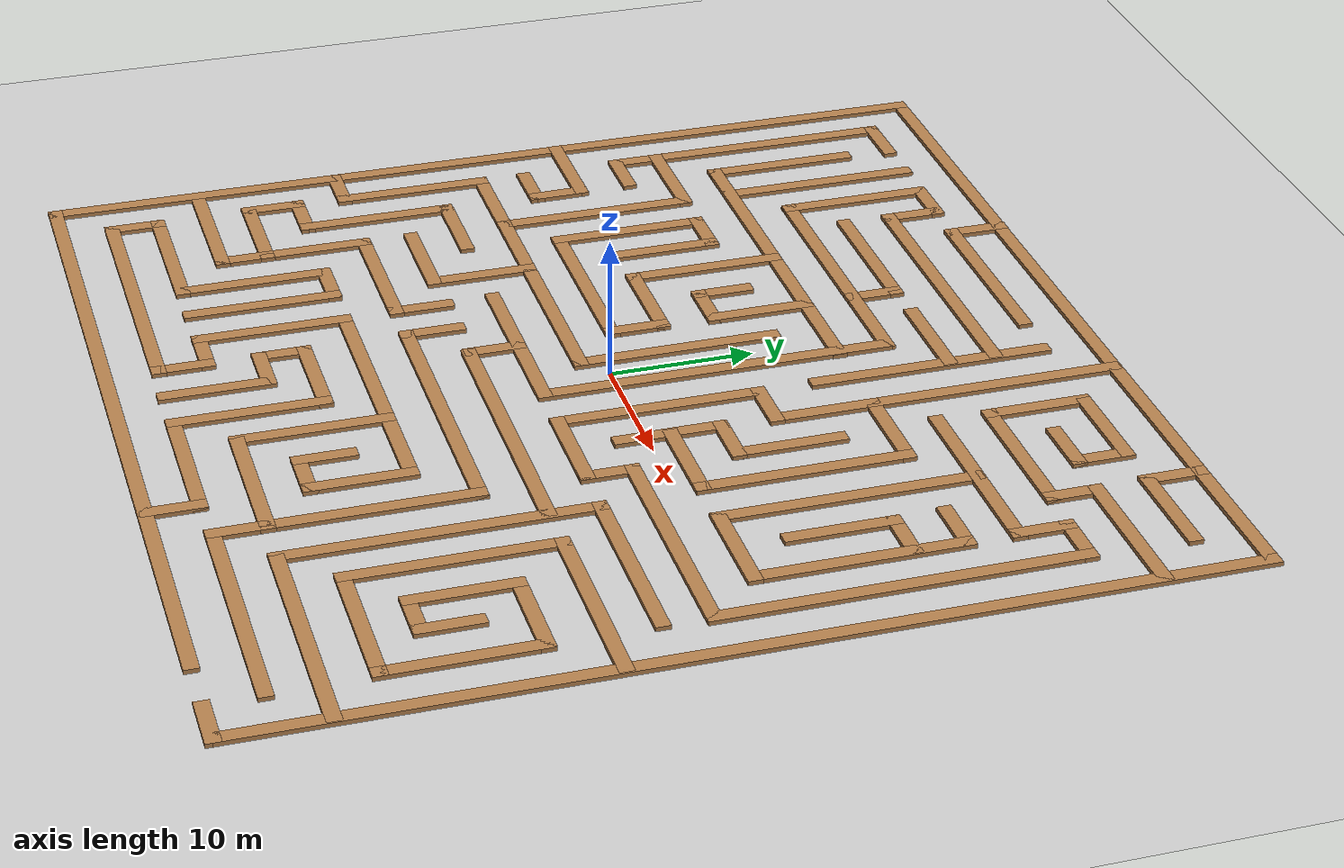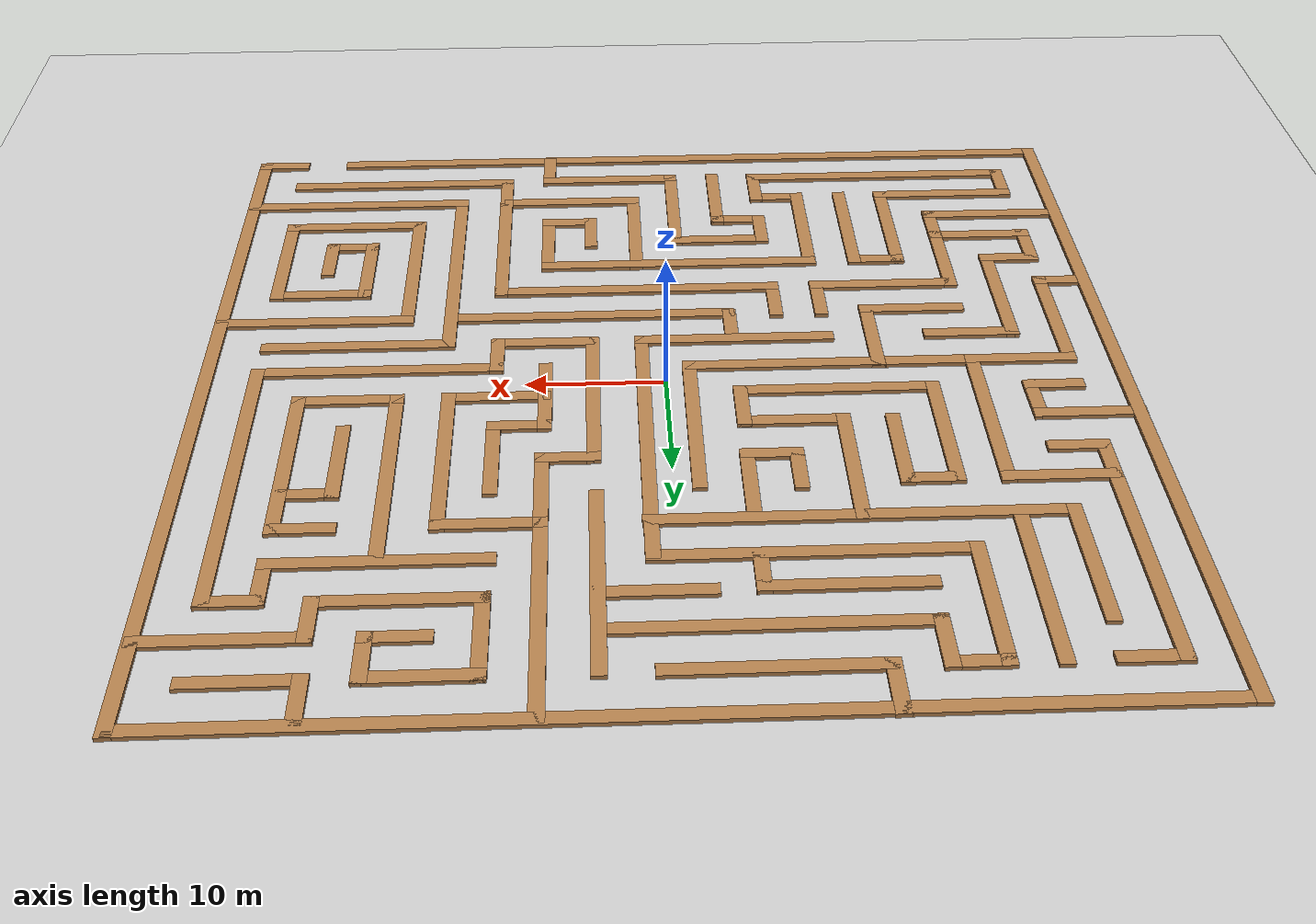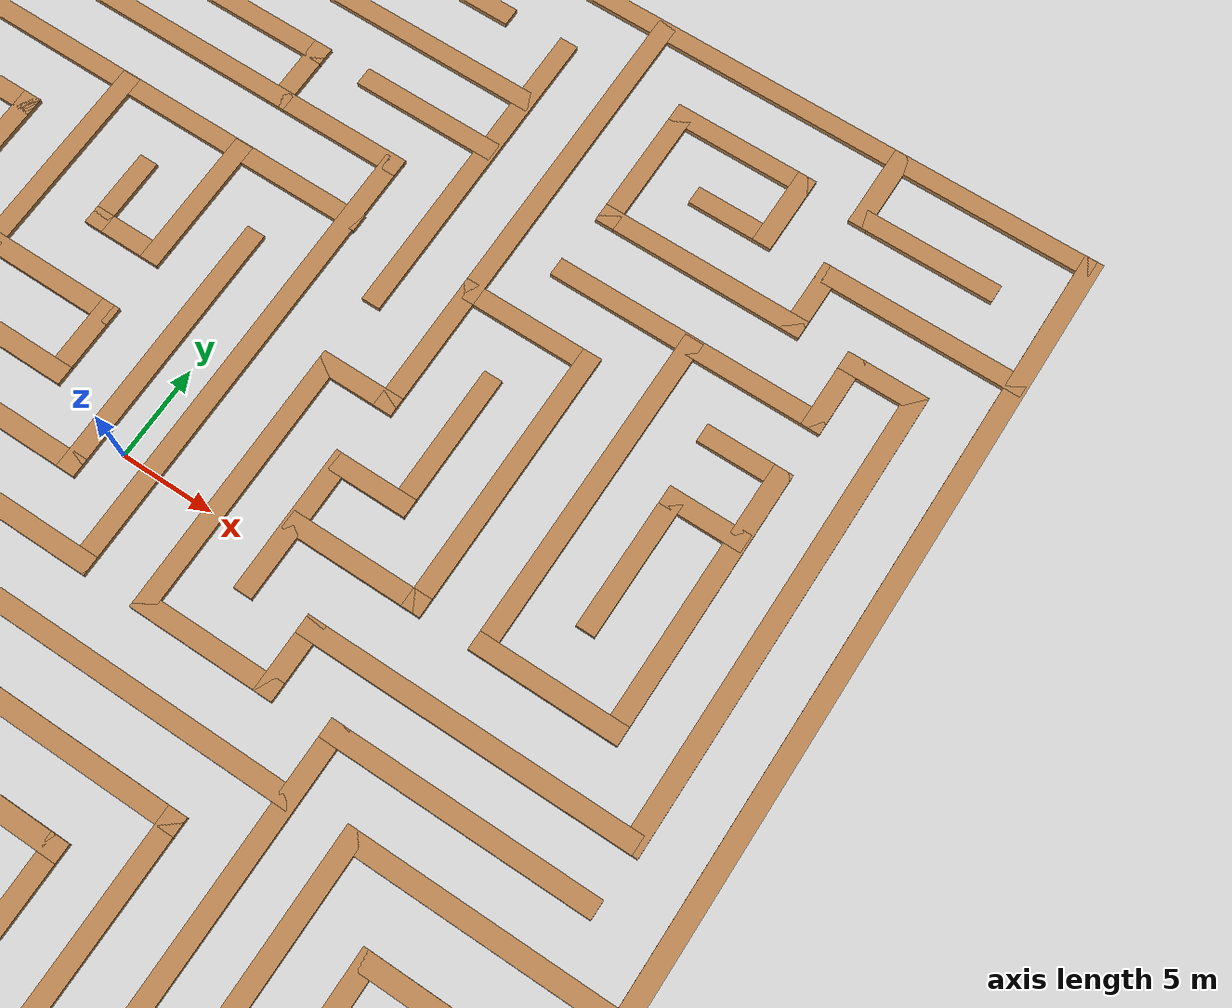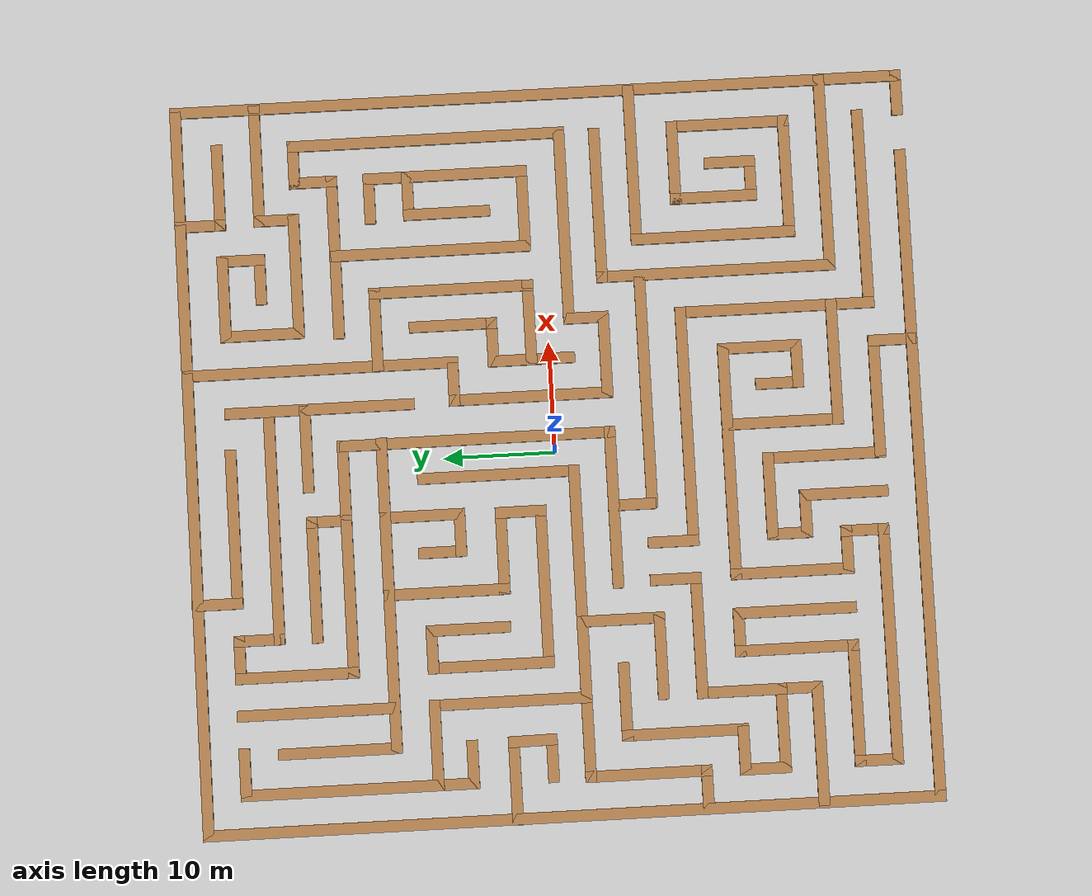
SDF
<sdf version="1.7">
 <world name="default">
  <light name="sun" type="directional">
   <pose>0 0 10 0 -0 0</pose>
   <diffuse>0.8 0.8 0.8 1</diffuse>
   <specular>0.2 0.2 0.2 1</specular>
   <attenuation>
    <range>1000</range>
    <constant>0.9</constant>
    <linear>0.01</linear>
    <quadratic>0.001</quadratic>
   </attenuation>
   <direction>-0.5 0.1 -0.9</direction>
   <spot><inner_angle>0</inner_angle><outer_angle>0</outer_angle><falloff>0</falloff></spot>
  </light>
  <model name="ground_plane">
   <static>1</static>
   <link name="link">
    <collision name="collision">
     <geometry><plane><normal>0 0 1</normal><size>100 100</size></plane></geometry>
     <surface><friction><ode><mu>100</mu><mu2>50</mu2></ode></friction></surface>
    </collision>
    <visual name="visual">
     <cast_shadows>0</cast_shadows>
     <geometry><plane><normal>0 0 1</normal><size>100 100</size></plane></geometry>
     <material>
      <script><uri>file://media/materials/scripts/gazebo.material</uri><name>Gazebo/Grey</name></script>
     </material>
    </visual>
   </link>
  </model>
  <gravity>0 0 -9.8</gravity>
  <magnetic_field>6e-06 2.3e-05 -4.2e-05</magnetic_field>
  <atmosphere type="adiabatic"/>
  <physics type="ode">
   <max_step_size>0.001</max_step_size>
   <real_time_factor>1</real_time_factor>
   <real_time_update_rate>1000</real_time_update_rate>
  </physics>
  <scene><ambient>0.4 0.4 0.4 1</ambient><background>0.7 0.7 0.7 1</background><shadows>1</shadows></scene>
  <audio><device>default</device></audio>
  <spherical_coordinates>
   <surface_model>EARTH_WGS84</surface_model>
   <latitude_deg>0</latitude_deg>
   <longitude_deg>0</longitude_deg>
   <elevation>0</elevation>
   <heading_deg>0</heading_deg>
  </spherical_coordinates>
  <model name="Maze_thick_walls">
   <pose>0.046124 0.012169 0 0 -0 0</pose>
   <link name="Wall_0">
    <collision name="Wall_0_Collision">
     <geometry><box><size>65.8498 1 0.3</size></box></geometry>
     <pose>0 0 0.15 0 -0 0</pose>
    </collision>
    <visual name="Wall_0_Visual">
     <pose>0 0 0.15 0 -0 0</pose>
     <geometry><box><size>65.8498 1 0.3</size></box></geometry>
     <material>
      <script><uri>file://media/materials/scripts/gazebo.material</uri><name>Gazebo/Wood</name></script>
      <ambient>1 1 1 1</ambient>
     </material>
     <meta><layer>0</layer></meta>
    </visual>
    <pose>-0.164124 32.6558 0 0 -0 0</pose>
   </link>
   <link name="Wall_10">
    <collision name="Wall_10_Collision">
     <geometry><box><size>66.3629 1 0.3</size></box></geometry>
     <pose>0 0 0.15 0 -0 0</pose>
    </collision>
    <visual name="Wall_10_Visual">
     <pose>0 0 0.15 0 -0 0</pose>
     <geometry><box><size>66.3629 1 0.3</size></box></geometry>
     <material>
      <script><uri>file://media/materials/scripts/gazebo.material</uri><name>Gazebo/Wood</name></script>
      <ambient>1 1 1 1</ambient>
     </material>
     <meta><layer>0</layer></meta>
    </visual>
    <pose>32.5818 -0.012722 0 0 -0 1.56973</pose>
   </link>
   <link name="Wall_101">
    <collision name="Wall_101_Collision">
     <geometry><box><size>14.6 1 0.3</size></box></geometry>
     <pose>0 0 0.15 0 -0 0</pose>
    </collision>
    <visual name="Wall_101_Visual">
     <pose>0 0 0.15 0 -0 0</pose>
     <geometry><box><size>14.6 1 0.3</size></box></geometry>
     <material>
      <script><uri>file://media/materials/scripts/gazebo.material</uri><name>Gazebo/Wood</name></script>
      <ambient>1 1 1 1</ambient>
     </material>
     <meta><layer>0</layer></meta>
    </visual>
    <pose>12.0029 -18.8182 0 0 -0 1.5708</pose>
   </link>
   <link name="Wall_103">
    <collision name="Wall_103_Collision">
     <geometry><box><size>17.8495 1 0.3</size></box></geometry>
     <pose>0 0 0.15 0 -0 0</pose>
    </collision>
    <visual name="Wall_103_Visual">
     <pose>0 0 0.15 0 -0 0</pose>
     <geometry><box><size>17.8495 1 0.3</size></box></geometry>
     <material>
      <script><uri>file://media/materials/scripts/gazebo.material</uri><name>Gazebo/Wood</name></script>
      <ambient>1 1 1 1</ambient>
     </material>
     <meta><layer>0</layer></meta>
    </visual>
    <pose>24.0399 -25.7352 0 0 -0 3.14159</pose>
   </link>
   <link name="Wall_105">
    <collision name="Wall_105_Collision">
     <geometry><box><size>14.6003 1 0.3</size></box></geometry>
     <pose>0 0 0.15 0 -0 0</pose>
    </collision>
    <visual name="Wall_105_Visual">
     <pose>0 0 0.15 0 -0 0</pose>
     <geometry><box><size>14.6003 1 0.3</size></box></geometry>
     <material>
      <script><uri>file://media/materials/scripts/gazebo.material</uri><name>Gazebo/Wood</name></script>
      <ambient>1 1 1 1</ambient>
     </material>
     <meta><layer>0</layer></meta>
    </visual>
    <pose>25.6609 -8.44317 0 0 -0 3.14159</pose>
   </link>
   <link name="Wall_107">
    <collision name="Wall_107_Collision">
     <geometry><box><size>14.85 1 0.3</size></box></geometry>
     <pose>0 0 0.15 0 -0 0</pose>
    </collision>
    <visual name="Wall_107_Visual">
     <pose>0 0 0.15 0 -0 0</pose>
     <geometry><box><size>14.85 1 0.3</size></box></geometry>
     <material>
      <script><uri>file://media/materials/scripts/gazebo.material</uri><name>Gazebo/Wood</name></script>
      <ambient>1 1 1 1</ambient>
     </material>
     <meta><layer>0</layer></meta>
    </visual>
    <pose>18.8609 -15.3682 0 0 -0 -1.5708</pose>
   </link>
   <link name="Wall_109">
    <collision name="Wall_109_Collision">
     <geometry><box><size>11.1 1 0.3</size></box></geometry>
     <pose>0 0 0.15 0 -0 0</pose>
    </collision>
    <visual name="Wall_109_Visual">
     <pose>0 0 0.15 0 -0 0</pose>
     <geometry><box><size>11.1 1 0.3</size></box></geometry>
     <material>
      <script><uri>file://media/materials/scripts/gazebo.material</uri><name>Gazebo/Wood</name></script>
      <ambient>1 1 1 1</ambient>
     </material>
     <meta><layer>0</layer></meta>
    </visual>
    <pose>23.9109 -22.2932 0 0 -0 0</pose>
   </link>
   <link name="Wall_111">
    <collision name="Wall_111_Collision">
     <geometry><box><size>11.1 1 0.3</size></box></geometry>
     <pose>0 0 0.15 0 -0 0</pose>
    </collision>
    <visual name="Wall_111_Visual">
     <pose>0 0 0.15 0 -0 0</pose>
     <geometry><box><size>11.1 1 0.3</size></box></geometry>
     <material>
      <script><uri>file://media/materials/scripts/gazebo.material</uri><name>Gazebo/Wood</name></script>
      <ambient>1 1 1 1</ambient>
     </material>
     <meta><layer>0</layer></meta>
    </visual>
    <pose>28.9609 -17.2432 0 0 -0 1.5708</pose>
   </link>
   <link name="Wall_113">
    <collision name="Wall_113_Collision">
     <geometry><box><size>7.6 1 0.3</size></box></geometry>
     <pose>0 0 0.15 0 -0 0</pose>
    </collision>
    <visual name="Wall_113_Visual">
     <pose>0 0 0.15 0 -0 0</pose>
     <geometry><box><size>7.6 1 0.3</size></box></geometry>
     <material>
      <script><uri>file://media/materials/scripts/gazebo.material</uri><name>Gazebo/Wood</name></script>
      <ambient>1 1 1 1</ambient>
     </material>
     <meta><layer>0</layer></meta>
    </visual>
    <pose>25.6609 -12.1932 0 0 -0 3.14159</pose>
   </link>
   <link name="Wall_115">
    <collision name="Wall_115_Collision">
     <geometry><box><size>7.85 1 0.3</size></box></geometry>
     <pose>0 0 0.15 0 -0 0</pose>
    </collision>
    <visual name="Wall_115_Visual">
     <pose>0 0 0.15 0 -0 0</pose>
     <geometry><box><size>7.85 1 0.3</size></box></geometry>
     <material>
      <script><uri>file://media/materials/scripts/gazebo.material</uri><name>Gazebo/Wood</name></script>
      <ambient>1 1 1 1</ambient>
     </material>
     <meta><layer>0</layer></meta>
    </visual>
    <pose>22.3609 -15.6182 0 0 -0 -1.5708</pose>
   </link>
   <link name="Wall_117">
    <collision name="Wall_117_Collision">
     <geometry><box><size>4.1 1 0.3</size></box></geometry>
     <pose>0 0 0.15 0 -0 0</pose>
    </collision>
    <visual name="Wall_117_Visual">
     <pose>0 0 0.15 0 -0 0</pose>
     <geometry><box><size>4.1 1 0.3</size></box></geometry>
     <material>
      <script><uri>file://media/materials/scripts/gazebo.material</uri><name>Gazebo/Wood</name></script>
      <ambient>1 1 1 1</ambient>
     </material>
     <meta><layer>0</layer></meta>
    </visual>
    <pose>23.9109 -19.0432 0 0 -0 0</pose>
   </link>
   <link name="Wall_119">
    <collision name="Wall_119_Collision">
     <geometry><box><size>4.6 1 0.3</size></box></geometry>
     <pose>0 0 0.15 0 -0 0</pose>
    </collision>
    <visual name="Wall_119_Visual">
     <pose>0 0 0.15 0 -0 0</pose>
     <geometry><box><size>4.6 1 0.3</size></box></geometry>
     <material>
      <script><uri>file://media/materials/scripts/gazebo.material</uri><name>Gazebo/Wood</name></script>
      <ambient>1 1 1 1</ambient>
     </material>
     <meta><layer>0</layer></meta>
    </visual>
    <pose>25.4609 -17.2432 0 0 -0 1.5708</pose>
   </link>
   <link name="Wall_123">
    <collision name="Wall_123_Collision">
     <geometry><box><size>21.6 1 0.3</size></box></geometry>
     <pose>0 0 0.15 0 -0 0</pose>
    </collision>
    <visual name="Wall_123_Visual">
     <pose>0 0 0.15 0 -0 0</pose>
     <geometry><box><size>21.6 1 0.3</size></box></geometry>
     <material>
      <script><uri>file://media/materials/scripts/gazebo.material</uri><name>Gazebo/Wood</name></script>
      <ambient>1 1 1 1</ambient>
     </material>
     <meta><layer>0</layer></meta>
    </visual>
    <pose>15.6149 -15.4352 0 0 -0 1.5708</pose>
   </link>
   <link name="Wall_125">
    <collision name="Wall_125_Collision">
     <geometry><box><size>14.1 1 0.3</size></box></geometry>
     <pose>0 0 0.15 0 -0 0</pose>
    </collision>
    <visual name="Wall_125_Visual">
     <pose>0 0 0.15 0 -0 0</pose>
     <geometry><box><size>14.1 1 0.3</size></box></geometry>
     <material>
      <script><uri>file://media/materials/scripts/gazebo.material</uri><name>Gazebo/Wood</name></script>
      <ambient>1 1 1 1</ambient>
     </material>
     <meta><layer>0</layer></meta>
    </visual>
    <pose>22.1649 -5.13517 0 0 -0 0</pose>
   </link>
   <link name="Wall_127">
    <collision name="Wall_127_Collision">
     <geometry><box><size>21.3502 1 0.3</size></box></geometry>
     <pose>0 0 0.15 0 -0 0</pose>
    </collision>
    <visual name="Wall_127_Visual">
     <pose>0 0 0.15 0 -0 0</pose>
     <geometry><box><size>21.3502 1 0.3</size></box></geometry>
     <material>
      <script><uri>file://media/materials/scripts/gazebo.material</uri><name>Gazebo/Wood</name></script>
      <ambient>1 1 1 1</ambient>
     </material>
     <meta><layer>0</layer></meta>
    </visual>
    <pose>5.22088 -8.50017 0 0 -0 3.14159</pose>
   </link>
   <link name="Wall_129">
    <collision name="Wall_129_Collision">
     <geometry><box><size>21.6 1 0.3</size></box></geometry>
     <pose>0 0 0.15 0 -0 0</pose>
    </collision>
    <visual name="Wall_129_Visual">
     <pose>0 0 0.15 0 -0 0</pose>
     <geometry><box><size>21.6 1 0.3</size></box></geometry>
     <material>
      <script><uri>file://media/materials/scripts/gazebo.material</uri><name>Gazebo/Wood</name></script>
      <ambient>1 1 1 1</ambient>
     </material>
     <meta><layer>0</layer></meta>
    </visual>
    <pose>1.70288 -12.0182 0 0 -0 3.14159</pose>
   </link>
   <link name="Wall_13">
    <collision name="Wall_13_Collision">
     <geometry><box><size>4.714 1 0.3</size></box></geometry>
     <pose>0 0 0.15 0 -0 0</pose>
    </collision>
    <visual name="Wall_13_Visual">
     <pose>0 0 0.15 0 -0 0</pose>
     <geometry><box><size>4.714 1 0.3</size></box></geometry>
     <material>
      <script><uri>file://media/materials/scripts/gazebo.material</uri><name>Gazebo/Wood</name></script>
      <ambient>1 1 1 1</ambient>
     </material>
     <meta><layer>0</layer></meta>
    </visual>
    <pose>-27.3391 29.1298 0 0 -0 3.14159</pose>
   </link>
   <link name="Wall_131">
    <collision name="Wall_131_Collision">
     <geometry><box><size>4.6 1 0.3</size></box></geometry>
     <pose>0 0 0.15 0 -0 0</pose>
    </collision>
    <visual name="Wall_131_Visual">
     <pose>0 0 0.15 0 -0 0</pose>
     <geometry><box><size>4.6 1 0.3</size></box></geometry>
     <material>
      <script><uri>file://media/materials/scripts/gazebo.material</uri><name>Gazebo/Wood</name></script>
      <ambient>1 1 1 1</ambient>
     </material>
     <meta><layer>0</layer></meta>
    </visual>
    <pose>-8.59712 -10.2182 0 0 -0 1.5708</pose>
   </link>
   <link name="Wall_133">
    <collision name="Wall_133_Collision">
     <geometry><box><size>4.6 1 0.3</size></box></geometry>
     <pose>0 0 0.15 0 -0 0</pose>
    </collision>
    <visual name="Wall_133_Visual">
     <pose>0 0 0.15 0 -0 0</pose>
     <geometry><box><size>4.6 1 0.3</size></box></geometry>
     <material>
      <script><uri>file://media/materials/scripts/gazebo.material</uri><name>Gazebo/Wood</name></script>
      <ambient>1 1 1 1</ambient>
     </material>
     <meta><layer>0</layer></meta>
    </visual>
    <pose>-11.9741 -10.2182 0 0 -0 -1.5708</pose>
   </link>
   <link name="Wall_135">
    <collision name="Wall_135_Collision">
     <geometry><box><size>11.321 1 0.3</size></box></geometry>
     <pose>0 0 0.15 0 -0 0</pose>
    </collision>
    <visual name="Wall_135_Visual">
     <pose>0 0 0.15 0 -0 0</pose>
     <geometry><box><size>11.321 1 0.3</size></box></geometry>
     <material>
      <script><uri>file://media/materials/scripts/gazebo.material</uri><name>Gazebo/Wood</name></script>
      <ambient>1 1 1 1</ambient>
     </material>
     <meta><layer>0</layer></meta>
    </visual>
    <pose>-17.1346 -12.0182 0 0 -0 3.14159</pose>
   </link>
   <link name="Wall_137">
    <collision name="Wall_137_Collision">
     <geometry><box><size>8.05106 1 0.3</size></box></geometry>
     <pose>0 0 0.15 0 -0 0</pose>
    </collision>
    <visual name="Wall_137_Visual">
     <pose>0 0 0.15 0 -0 0</pose>
     <geometry><box><size>8.05106 1 0.3</size></box></geometry>
     <material>
      <script><uri>file://media/materials/scripts/gazebo.material</uri><name>Gazebo/Wood</name></script>
      <ambient>1 1 1 1</ambient>
     </material>
     <meta><layer>0</layer></meta>
    </visual>
    <pose>-22.2951 -15.5437 0 0 -0 -1.5708</pose>
   </link>
   <link name="Wall_139">
    <collision name="Wall_139_Collision">
     <geometry><box><size>7.84983 1 0.3</size></box></geometry>
     <pose>0 0 0.15 0 -0 0</pose>
    </collision>
    <visual name="Wall_139_Visual">
     <pose>0 0 0.15 0 -0 0</pose>
     <geometry><box><size>7.84983 1 0.3</size></box></geometry>
     <material>
      <script><uri>file://media/materials/scripts/gazebo.material</uri><name>Gazebo/Wood</name></script>
      <ambient>1 1 1 1</ambient>
     </material>
     <meta><layer>0</layer></meta>
    </visual>
    <pose>-18.7611 -8.54617 0 0 -0 0</pose>
   </link>
   <link name="Wall_141">
    <collision name="Wall_141_Collision">
     <geometry><box><size>7.898 1 0.3</size></box></geometry>
     <pose>0 0 0.15 0 -0 0</pose>
    </collision>
    <visual name="Wall_141_Visual">
     <pose>0 0 0.15 0 -0 0</pose>
     <geometry><box><size>7.898 1 0.3</size></box></geometry>
     <material>
      <script><uri>file://media/materials/scripts/gazebo.material</uri><name>Gazebo/Wood</name></script>
      <ambient>1 1 1 1</ambient>
     </material>
     <meta><layer>0</layer></meta>
    </visual>
    <pose>-15.3361 -5.09717 0 0 -0 1.5708</pose>
   </link>
   <link name="Wall_143">
    <collision name="Wall_143_Collision">
     <geometry><box><size>14.5998 1 0.3</size></box></geometry>
     <pose>0 0 0.15 0 -0 0</pose>
    </collision>
    <visual name="Wall_143_Visual">
     <pose>0 0 0.15 0 -0 0</pose>
     <geometry><box><size>14.5998 1 0.3</size></box></geometry>
     <material>
      <script><uri>file://media/materials/scripts/gazebo.material</uri><name>Gazebo/Wood</name></script>
      <ambient>1 1 1 1</ambient>
     </material>
     <meta><layer>0</layer></meta>
    </visual>
    <pose>-5.22012 -5.05017 0 0 -0 0</pose>
   </link>
   <link name="Wall_145">
    <collision name="Wall_145_Collision">
     <geometry><box><size>4.278 1 0.3</size></box></geometry>
     <pose>0 0 0.15 0 -0 0</pose>
    </collision>
    <visual name="Wall_145_Visual">
     <pose>0 0 0.15 0 -0 0</pose>
     <geometry><box><size>4.278 1 0.3</size></box></geometry>
     <material>
      <script><uri>file://media/materials/scripts/gazebo.material</uri><name>Gazebo/Wood</name></script>
      <ambient>1 1 1 1</ambient>
     </material>
     <meta><layer>0</layer></meta>
    </visual>
    <pose>-5.07412 -6.71517 0 0 -0 -1.5708</pose>
   </link>
   <link name="Wall_147">
    <collision name="Wall_147_Collision">
     <geometry><box><size>7.75817 1 0.3</size></box></geometry>
     <pose>0 0 0.15 0 -0 0</pose>
    </collision>
    <visual name="Wall_147_Visual">
     <pose>0 0 0.15 0 -0 0</pose>
     <geometry><box><size>7.75817 1 0.3</size></box></geometry>
     <material>
      <script><uri>file://media/materials/scripts/gazebo.material</uri><name>Gazebo/Wood</name></script>
      <ambient>1 1 1 1</ambient>
     </material>
     <meta><layer>0</layer></meta>
    </visual>
    <pose>-18.7151 -1.64817 0 0 -0 3.14159</pose>
   </link>
   <link name="Wall_149">
    <collision name="Wall_149_Collision">
     <geometry><box><size>14.6 1 0.3</size></box></geometry>
     <pose>0 0 0.15 0 -0 0</pose>
    </collision>
    <visual name="Wall_149_Visual">
     <pose>0 0 0.15 0 -0 0</pose>
     <geometry><box><size>14.6 1 0.3</size></box></geometry>
     <material>
      <script><uri>file://media/materials/scripts/gazebo.material</uri><name>Gazebo/Wood</name></script>
      <ambient>1 1 1 1</ambient>
     </material>
     <meta><layer>0</layer></meta>
    </visual>
    <pose>-8.53612 -1.64817 0 0 -0 0</pose>
   </link>
   <link name="Wall_15">
    <collision name="Wall_15_Collision">
     <geometry><box><size>21.35 1 0.3</size></box></geometry>
     <pose>0 0 0.15 0 -0 0</pose>
    </collision>
    <visual name="Wall_15_Visual">
     <pose>0 0 0.15 0 -0 0</pose>
     <geometry><box><size>21.35 1 0.3</size></box></geometry>
     <material>
      <script><uri>file://media/materials/scripts/gazebo.material</uri><name>Gazebo/Wood</name></script>
      <ambient>1 1 1 1</ambient>
     </material>
     <meta><layer>0</layer></meta>
    </visual>
    <pose>-29.1961 18.9548 0 0 -0 -1.5708</pose>
   </link>
   <link name="Wall_151">
    <collision name="Wall_151_Collision">
     <geometry><box><size>14.6 1 0.3</size></box></geometry>
     <pose>0 0 0.15 0 -0 0</pose>
    </collision>
    <visual name="Wall_151_Visual">
     <pose>0 0 0.15 0 -0 0</pose>
     <geometry><box><size>14.6 1 0.3</size></box></geometry>
     <material>
      <script><uri>file://media/materials/scripts/gazebo.material</uri><name>Gazebo/Wood</name></script>
      <ambient>1 1 1 1</ambient>
     </material>
     <meta><layer>0</layer></meta>
    </visual>
    <pose>-1.73612 5.15183 0 0 -0 1.5708</pose>
   </link>
   <link name="Wall_153">
    <collision name="Wall_153_Collision">
     <geometry><box><size>7.84995 1 0.3</size></box></geometry>
     <pose>0 0 0.15 0 -0 0</pose>
    </collision>
    <visual name="Wall_153_Visual">
     <pose>0 0 0.15 0 -0 0</pose>
     <geometry><box><size>7.84995 1 0.3</size></box></geometry>
     <material>
      <script><uri>file://media/materials/scripts/gazebo.material</uri><name>Gazebo/Wood</name></script>
      <ambient>1 1 1 1</ambient>
     </material>
     <meta><layer>0</layer></meta>
    </visual>
    <pose>8.59088 -5.05017 0 0 -0 0</pose>
   </link>
   <link name="Wall_155">
    <collision name="Wall_155_Collision">
     <geometry><box><size>4.1 1 0.3</size></box></geometry>
     <pose>0 0 0.15 0 -0 0</pose>
    </collision>
    <visual name="Wall_155_Visual">
     <pose>0 0 0.15 0 -0 0</pose>
     <geometry><box><size>4.1 1 0.3</size></box></geometry>
     <material>
      <script><uri>file://media/materials/scripts/gazebo.material</uri><name>Gazebo/Wood</name></script>
      <ambient>1 1 1 1</ambient>
     </material>
     <meta><layer>0</layer></meta>
    </visual>
    <pose>12.0159 -3.50017 0 0 -0 1.5708</pose>
   </link>
   <link name="Wall_157">
    <collision name="Wall_157_Collision">
     <geometry><box><size>17.699 1 0.3</size></box></geometry>
     <pose>0 0 0.15 0 -0 0</pose>
    </collision>
    <visual name="Wall_157_Visual">
     <pose>0 0 0.15 0 -0 0</pose>
     <geometry><box><size>17.699 1 0.3</size></box></geometry>
     <material>
      <script><uri>file://media/materials/scripts/gazebo.material</uri><name>Gazebo/Wood</name></script>
      <ambient>1 1 1 1</ambient>
     </material>
     <meta><layer>0</layer></meta>
    </visual>
    <pose>20.3654 -1.95017 0 0 -0 0</pose>
   </link>
   <link name="Wall_159">
    <collision name="Wall_159_Collision">
     <geometry><box><size>25.1 1 0.3</size></box></geometry>
     <pose>0 0 0.15 0 -0 0</pose>
    </collision>
    <visual name="Wall_159_Visual">
     <pose>0 0 0.15 0 -0 0</pose>
     <geometry><box><size>25.1 1 0.3</size></box></geometry>
     <material>
      <script><uri>file://media/materials/scripts/gazebo.material</uri><name>Gazebo/Wood</name></script>
      <ambient>1 1 1 1</ambient>
     </material>
     <meta><layer>0</layer></meta>
    </visual>
    <pose>29.0099 10.1139 0 0 -0 1.5708</pose>
   </link>
   <link name="Wall_161">
    <collision name="Wall_161_Collision">
     <geometry><box><size>4.35 1 0.3</size></box></geometry>
     <pose>0 0 0.15 0 -0 0</pose>
    </collision>
    <visual name="Wall_161_Visual">
     <pose>0 0 0.15 0 -0 0</pose>
     <geometry><box><size>4.35 1 0.3</size></box></geometry>
     <material>
      <script><uri>file://media/materials/scripts/gazebo.material</uri><name>Gazebo/Wood</name></script>
      <ambient>1 1 1 1</ambient>
     </material>
     <meta><layer>0</layer></meta>
    </visual>
    <pose>27.3349 22.1638 0 0 -0 3.14159</pose>
   </link>
   <link name="Wall_163">
    <collision name="Wall_163_Collision">
     <geometry><box><size>4.35 1 0.3</size></box></geometry>
     <pose>0 0 0.15 0 -0 0</pose>
    </collision>
    <visual name="Wall_163_Visual">
     <pose>0 0 0.15 0 -0 0</pose>
     <geometry><box><size>4.35 1 0.3</size></box></geometry>
     <material>
      <script><uri>file://media/materials/scripts/gazebo.material</uri><name>Gazebo/Wood</name></script>
      <ambient>1 1 1 1</ambient>
     </material>
     <meta><layer>0</layer></meta>
    </visual>
    <pose>25.6599 20.4888 0 0 -0 -1.5708</pose>
   </link>
   <link name="Wall_165">
    <collision name="Wall_165_Collision">
     <geometry><box><size>14.85 1 0.3</size></box></geometry>
     <pose>0 0 0.15 0 -0 0</pose>
    </collision>
    <visual name="Wall_165_Visual">
     <pose>0 0 0.15 0 -0 0</pose>
     <geometry><box><size>14.85 1 0.3</size></box></geometry>
     <material>
      <script><uri>file://media/materials/scripts/gazebo.material</uri><name>Gazebo/Wood</name></script>
      <ambient>1 1 1 1</ambient>
     </material>
     <meta><layer>0</layer></meta>
    </visual>
    <pose>18.7349 18.8138 0 0 -0 3.14159</pose>
   </link>
   <link name="Wall_167">
    <collision name="Wall_167_Collision">
     <geometry><box><size>4.59954 1 0.3</size></box></geometry>
     <pose>0 0 0.15 0 -0 0</pose>
    </collision>
    <visual name="Wall_167_Visual">
     <pose>0 0 0.15 0 -0 0</pose>
     <geometry><box><size>4.59954 1 0.3</size></box></geometry>
     <material>
      <script><uri>file://media/materials/scripts/gazebo.material</uri><name>Gazebo/Wood</name></script>
      <ambient>1 1 1 1</ambient>
     </material>
     <meta><layer>0</layer></meta>
    </visual>
    <pose>23.8789 15.4688 0 0 -0 0</pose>
   </link>
   <link name="Wall_169">
    <collision name="Wall_169_Collision">
     <geometry><box><size>14.85 1 0.3</size></box></geometry>
     <pose>0 0 0.15 0 -0 0</pose>
    </collision>
    <visual name="Wall_169_Visual">
     <pose>0 0 0.15 0 -0 0</pose>
     <geometry><box><size>14.85 1 0.3</size></box></geometry>
     <material>
      <script><uri>file://media/materials/scripts/gazebo.material</uri><name>Gazebo/Wood</name></script>
      <ambient>1 1 1 1</ambient>
     </material>
     <meta><layer>0</layer></meta>
    </visual>
    <pose>25.6789 8.54383 0 0 -0 -1.5708</pose>
   </link>
   <link name="Wall_17">
    <collision name="Wall_17_Collision">
     <geometry><box><size>4.35 1 0.3</size></box></geometry>
     <pose>0 0 0.15 0 -0 0</pose>
    </collision>
    <visual name="Wall_17_Visual">
     <pose>0 0 0.15 0 -0 0</pose>
     <geometry><box><size>4.35 1 0.3</size></box></geometry>
     <material>
      <script><uri>file://media/materials/scripts/gazebo.material</uri><name>Gazebo/Wood</name></script>
      <ambient>1 1 1 1</ambient>
     </material>
     <meta><layer>0</layer></meta>
    </visual>
    <pose>-27.5211 8.77983 0 0 -0 0</pose>
   </link>
   <link name="Wall_171">
    <collision name="Wall_171_Collision">
     <geometry><box><size>4.35026 1 0.3</size></box></geometry>
     <pose>0 0 0.15 0 -0 0</pose>
    </collision>
    <visual name="Wall_171_Visual">
     <pose>0 0 0.15 0 -0 0</pose>
     <geometry><box><size>4.35026 1 0.3</size></box></geometry>
     <material>
      <script><uri>file://media/materials/scripts/gazebo.material</uri><name>Gazebo/Wood</name></script>
      <ambient>1 1 1 1</ambient>
     </material>
     <meta><layer>0</layer></meta>
    </visual>
    <pose>23.8999 11.9818 0 0 -0 3.14159</pose>
   </link>
   <link name="Wall_173">
    <collision name="Wall_173_Collision">
     <geometry><box><size>7.85 1 0.3</size></box></geometry>
     <pose>0 0 0.15 0 -0 0</pose>
    </collision>
    <visual name="Wall_173_Visual">
     <pose>0 0 0.15 0 -0 0</pose>
     <geometry><box><size>7.85 1 0.3</size></box></geometry>
     <material>
      <script><uri>file://media/materials/scripts/gazebo.material</uri><name>Gazebo/Wood</name></script>
      <ambient>1 1 1 1</ambient>
     </material>
     <meta><layer>0</layer></meta>
    </visual>
    <pose>22.2249 8.55683 0 0 -0 -1.5708</pose>
   </link>
   <link name="Wall_175">
    <collision name="Wall_175_Collision">
     <geometry><box><size>7.85 1 0.3</size></box></geometry>
     <pose>0 0 0.15 0 -0 0</pose>
    </collision>
    <visual name="Wall_175_Visual">
     <pose>0 0 0.15 0 -0 0</pose>
     <geometry><box><size>7.85 1 0.3</size></box></geometry>
     <material>
      <script><uri>file://media/materials/scripts/gazebo.material</uri><name>Gazebo/Wood</name></script>
      <ambient>1 1 1 1</ambient>
     </material>
     <meta><layer>0</layer></meta>
    </visual>
    <pose>22.2539 1.61883 0 0 -0 3.14159</pose>
   </link>
   <link name="Wall_177">
    <collision name="Wall_177_Collision">
     <geometry><box><size>18.1 1 0.3</size></box></geometry>
     <pose>0 0 0.15 0 -0 0</pose>
    </collision>
    <visual name="Wall_177_Visual">
     <pose>0 0 0.15 0 -0 0</pose>
     <geometry><box><size>18.1 1 0.3</size></box></geometry>
     <material>
      <script><uri>file://media/materials/scripts/gazebo.material</uri><name>Gazebo/Wood</name></script>
      <ambient>1 1 1 1</ambient>
     </material>
     <meta><layer>0</layer></meta>
    </visual>
    <pose>18.8289 10.1688 0 0 -0 1.5708</pose>
   </link>
   <link name="Wall_179">
    <collision name="Wall_179_Collision">
     <geometry><box><size>7.85039 1 0.3</size></box></geometry>
     <pose>0 0 0.15 0 -0 0</pose>
    </collision>
    <visual name="Wall_179_Visual">
     <pose>0 0 0.15 0 -0 0</pose>
     <geometry><box><size>7.85039 1 0.3</size></box></geometry>
     <material>
      <script><uri>file://media/materials/scripts/gazebo.material</uri><name>Gazebo/Wood</name></script>
      <ambient>1 1 1 1</ambient>
     </material>
     <meta><layer>0</layer></meta>
    </visual>
    <pose>8.50888 1.61983 0 0 -0 1.5708</pose>
   </link>
   <link name="Wall_181">
    <collision name="Wall_181_Collision">
     <geometry><box><size>7.59964 1 0.3</size></box></geometry>
     <pose>0 0 0.15 0 -0 0</pose>
    </collision>
    <visual name="Wall_181_Visual">
     <pose>0 0 0.15 0 -0 0</pose>
     <geometry><box><size>7.59964 1 0.3</size></box></geometry>
     <material>
      <script><uri>file://media/materials/scripts/gazebo.material</uri><name>Gazebo/Wood</name></script>
      <ambient>1 1 1 1</ambient>
     </material>
     <meta><layer>0</layer></meta>
    </visual>
    <pose>11.9409 1.61383 0 0 -0 0</pose>
   </link>
   <link name="Wall_183">
    <collision name="Wall_183_Collision">
     <geometry><box><size>14.85 1 0.3</size></box></geometry>
     <pose>0 0 0.15 0 -0 0</pose>
    </collision>
    <visual name="Wall_183_Visual">
     <pose>0 0 0.15 0 -0 0</pose>
     <geometry><box><size>14.85 1 0.3</size></box></geometry>
     <material>
      <script><uri>file://media/materials/scripts/gazebo.material</uri><name>Gazebo/Wood</name></script>
      <ambient>1 1 1 1</ambient>
     </material>
     <meta><layer>0</layer></meta>
    </visual>
    <pose>15.2409 8.53883 0 0 -0 1.5708</pose>
   </link>
   <link name="Wall_185">
    <collision name="Wall_185_Collision">
     <geometry><box><size>7.6 1 0.3</size></box></geometry>
     <pose>0 0 0.15 0 -0 0</pose>
    </collision>
    <visual name="Wall_185_Visual">
     <pose>0 0 0.15 0 -0 0</pose>
     <geometry><box><size>7.6 1 0.3</size></box></geometry>
     <material>
      <script><uri>file://media/materials/scripts/gazebo.material</uri><name>Gazebo/Wood</name></script>
      <ambient>1 1 1 1</ambient>
     </material>
     <meta><layer>0</layer></meta>
    </visual>
    <pose>11.9409 15.4638 0 0 -0 3.14159</pose>
   </link>
   <link name="Wall_187">
    <collision name="Wall_187_Collision">
     <geometry><box><size>7.724 1 0.3</size></box></geometry>
     <pose>0 0 0.15 0 -0 0</pose>
    </collision>
    <visual name="Wall_187_Visual">
     <pose>0 0 0.15 0 -0 0</pose>
     <geometry><box><size>7.724 1 0.3</size></box></geometry>
     <material>
      <script><uri>file://media/materials/scripts/gazebo.material</uri><name>Gazebo/Wood</name></script>
      <ambient>1 1 1 1</ambient>
     </material>
     <meta><layer>0</layer></meta>
    </visual>
    <pose>8.64088 12.1018 0 0 -0 -1.5708</pose>
   </link>
   <link name="Wall_189">
    <collision name="Wall_189_Collision">
     <geometry><box><size>7.944 1 0.3</size></box></geometry>
     <pose>0 0 0.15 0 -0 0</pose>
    </collision>
    <visual name="Wall_189_Visual">
     <pose>0 0 0.15 0 -0 0</pose>
     <geometry><box><size>7.944 1 0.3</size></box></geometry>
     <material>
      <script><uri>file://media/materials/scripts/gazebo.material</uri><name>Gazebo/Wood</name></script>
      <ambient>1 1 1 1</ambient>
     </material>
     <meta><layer>0</layer></meta>
    </visual>
    <pose>11.9899 8.51683 0 0 -0 -1.5708</pose>
   </link>
   <link name="Wall_19">
    <collision name="Wall_19_Collision">
     <geometry><box><size>7.89642 1 0.3</size></box></geometry>
     <pose>0 0 0.15 0 -0 0</pose>
    </collision>
    <visual name="Wall_19_Visual">
     <pose>0 0 0.15 0 -0 0</pose>
     <geometry><box><size>7.89642 1 0.3</size></box></geometry>
     <material>
      <script><uri>file://media/materials/scripts/gazebo.material</uri><name>Gazebo/Wood</name></script>
      <ambient>1 1 1 1</ambient>
     </material>
     <meta><layer>0</layer></meta>
    </visual>
    <pose>-29.1691 5.05883 0 0 -0 0</pose>
   </link>
   <link name="Wall_191">
    <collision name="Wall_191_Collision">
     <geometry><box><size>4.481 1 0.3</size></box></geometry>
     <pose>0 0 0.15 0 -0 0</pose>
    </collision>
    <visual name="Wall_191_Visual">
     <pose>0 0 0.15 0 -0 0</pose>
     <geometry><box><size>4.481 1 0.3</size></box></geometry>
     <material>
      <script><uri>file://media/materials/scripts/gazebo.material</uri><name>Gazebo/Wood</name></script>
      <ambient>1 1 1 1</ambient>
     </material>
     <meta><layer>0</layer></meta>
    </visual>
    <pose>10.2494 5.04483 0 0 -0 3.14159</pose>
   </link>
   <link name="Wall_193">
    <collision name="Wall_193_Collision">
     <geometry><box><size>24.85 1 0.3</size></box></geometry>
     <pose>0 0 0.15 0 -0 0</pose>
    </collision>
    <visual name="Wall_193_Visual">
     <pose>0 0 0.15 0 -0 0</pose>
     <geometry><box><size>24.85 1 0.3</size></box></geometry>
     <material>
      <script><uri>file://media/materials/scripts/gazebo.material</uri><name>Gazebo/Wood</name></script>
      <ambient>1 1 1 1</ambient>
     </material>
     <meta><layer>0</layer></meta>
    </visual>
    <pose>1.57988 6.87483 0 0 -0 1.5708</pose>
   </link>
   <link name="Wall_195">
    <collision name="Wall_195_Collision">
     <geometry><box><size>14.79 1 0.3</size></box></geometry>
     <pose>0 0 0.15 0 -0 0</pose>
    </collision>
    <visual name="Wall_195_Visual">
     <pose>0 0 0.15 0 -0 0</pose>
     <geometry><box><size>14.79 1 0.3</size></box></geometry>
     <material>
      <script><uri>file://media/materials/scripts/gazebo.material</uri><name>Gazebo/Wood</name></script>
      <ambient>1 1 1 1</ambient>
     </material>
     <meta><layer>0</layer></meta>
    </visual>
    <pose>5.16588 1.84483 0 0 -0 1.5708</pose>
   </link>
   <link name="Wall_197">
    <collision name="Wall_197_Collision">
     <geometry><box><size>4.47552 1 0.3</size></box></geometry>
     <pose>0 0 0.15 0 -0 0</pose>
    </collision>
    <visual name="Wall_197_Visual">
     <pose>0 0 0.15 0 -0 0</pose>
     <geometry><box><size>4.47552 1 0.3</size></box></geometry>
     <material>
      <script><uri>file://media/materials/scripts/gazebo.material</uri><name>Gazebo/Wood</name></script>
      <ambient>1 1 1 1</ambient>
     </material>
     <meta><layer>0</layer></meta>
    </visual>
    <pose>6.90338 8.73983 0 0 -0 0</pose>
   </link>
   <link name="Wall_199">
    <collision name="Wall_199_Collision">
     <geometry><box><size>17.0997 1 0.3</size></box></geometry>
     <pose>0 0 0.15 0 -0 0</pose>
    </collision>
    <visual name="Wall_199_Visual">
     <pose>0 0 0.15 0 -0 0</pose>
     <geometry><box><size>17.0997 1 0.3</size></box></geometry>
     <material>
      <script><uri>file://media/materials/scripts/gazebo.material</uri><name>Gazebo/Wood</name></script>
      <ambient>1 1 1 1</ambient>
     </material>
     <meta><layer>0</layer></meta>
    </visual>
    <pose>5.05888 20.9058 0 0 -0 1.5708</pose>
   </link>
   <link name="Wall_2">
    <collision name="Wall_2_Collision">
     <geometry><box><size>66.35 1 0.3</size></box></geometry>
     <pose>0 0 0.15 0 -0 0</pose>
    </collision>
    <visual name="Wall_2_Visual">
     <pose>0 0 0.15 0 -0 0</pose>
     <geometry><box><size>66.35 1 0.3</size></box></geometry>
     <material>
      <script><uri>file://media/materials/scripts/gazebo.material</uri><name>Gazebo/Wood</name></script>
      <ambient>1 1 1 1</ambient>
     </material>
     <meta><layer>0</layer></meta>
    </visual>
    <pose>-32.5891 -0.019169 0 0 -0 -1.5708</pose>
   </link>
   <link name="Wall_201">
    <collision name="Wall_201_Collision">
     <geometry><box><size>7.84994 1 0.3</size></box></geometry>
     <pose>0 0 0.15 0 -0 0</pose>
    </collision>
    <visual name="Wall_201_Visual">
     <pose>0 0 0.15 0 -0 0</pose>
     <geometry><box><size>7.84994 1 0.3</size></box></geometry>
     <material>
      <script><uri>file://media/materials/scripts/gazebo.material</uri><name>Gazebo/Wood</name></script>
      <ambient>1 1 1 1</ambient>
     </material>
     <meta><layer>0</layer></meta>
    </visual>
    <pose>1.49488 22.2468 0 0 -0 3.14159</pose>
   </link>
   <link name="Wall_203">
    <collision name="Wall_203_Collision">
     <geometry><box><size>18.1 1 0.3</size></box></geometry>
     <pose>0 0 0.15 0 -0 0</pose>
    </collision>
    <visual name="Wall_203_Visual">
     <pose>0 0 0.15 0 -0 0</pose>
     <geometry><box><size>18.1 1 0.3</size></box></geometry>
     <material>
      <script><uri>file://media/materials/scripts/gazebo.material</uri><name>Gazebo/Wood</name></script>
      <ambient>1 1 1 1</ambient>
     </material>
     <meta><layer>0</layer></meta>
    </visual>
    <pose>8.64088 24.0138 0 0 -0 1.5708</pose>
   </link>
   <link name="Wall_207">
    <collision name="Wall_207_Collision">
     <geometry><box><size>4.60043 1 0.3</size></box></geometry>
     <pose>0 0 0.15 0 -0 0</pose>
    </collision>
    <visual name="Wall_207_Visual">
     <pose>0 0 0.15 0 -0 0</pose>
     <geometry><box><size>4.60043 1 0.3</size></box></geometry>
     <material>
      <script><uri>file://media/materials/scripts/gazebo.material</uri><name>Gazebo/Wood</name></script>
      <ambient>1 1 1 1</ambient>
     </material>
     <meta><layer>0</layer></meta>
    </visual>
    <pose>22.2059 30.8448 0 0 -0 -1.5708</pose>
   </link>
   <link name="Wall_209">
    <collision name="Wall_209_Collision">
     <geometry><box><size>7.85 1 0.3</size></box></geometry>
     <pose>0 0 0.15 0 -0 0</pose>
    </collision>
    <visual name="Wall_209_Visual">
     <pose>0 0 0.15 0 -0 0</pose>
     <geometry><box><size>7.85 1 0.3</size></box></geometry>
     <material>
      <script><uri>file://media/materials/scripts/gazebo.material</uri><name>Gazebo/Wood</name></script>
      <ambient>1 1 1 1</ambient>
     </material>
     <meta><layer>0</layer></meta>
    </visual>
    <pose>25.6309 29.0448 0 0 -0 0</pose>
   </link>
   <link name="Wall_21">
    <collision name="Wall_21_Collision">
     <geometry><box><size>4.39658 1 0.3</size></box></geometry>
     <pose>0 0 0.15 0 -0 0</pose>
    </collision>
    <visual name="Wall_21_Visual">
     <pose>0 0 0.15 0 -0 0</pose>
     <geometry><box><size>4.39658 1 0.3</size></box></geometry>
     <material>
      <script><uri>file://media/materials/scripts/gazebo.material</uri><name>Gazebo/Wood</name></script>
      <ambient>1 1 1 1</ambient>
     </material>
     <meta><layer>0</layer></meta>
    </visual>
    <pose>-25.6976 3.36083 0 0 -0 -1.55696</pose>
   </link>
   <link name="Wall_211">
    <collision name="Wall_211_Collision">
     <geometry><box><size>11.1001 1 0.3</size></box></geometry>
     <pose>0 0 0.15 0 -0 0</pose>
    </collision>
    <visual name="Wall_211_Visual">
     <pose>0 0 0.15 0 -0 0</pose>
     <geometry><box><size>11.1001 1 0.3</size></box></geometry>
     <material>
      <script><uri>file://media/materials/scripts/gazebo.material</uri><name>Gazebo/Wood</name></script>
      <ambient>1 1 1 1</ambient>
     </material>
     <meta><layer>0</layer></meta>
    </visual>
    <pose>27.4259 25.5138 0 0 -0 3.14159</pose>
   </link>
   <link name="Wall_213">
    <collision name="Wall_213_Collision">
     <geometry><box><size>4.1 1 0.3</size></box></geometry>
     <pose>0 0 0.15 0 -0 0</pose>
    </collision>
    <visual name="Wall_213_Visual">
     <pose>0 0 0.15 0 -0 0</pose>
     <geometry><box><size>4.1 1 0.3</size></box></geometry>
     <material>
      <script><uri>file://media/materials/scripts/gazebo.material</uri><name>Gazebo/Wood</name></script>
      <ambient>1 1 1 1</ambient>
     </material>
     <meta><layer>0</layer></meta>
    </visual>
    <pose>22.3759 23.9638 0 0 -0 -1.5708</pose>
   </link>
   <link name="Wall_215">
    <collision name="Wall_215_Collision">
     <geometry><box><size>11.35 1 0.3</size></box></geometry>
     <pose>0 0 0.15 0 -0 0</pose>
    </collision>
    <visual name="Wall_215_Visual">
     <pose>0 0 0.15 0 -0 0</pose>
     <geometry><box><size>11.35 1 0.3</size></box></geometry>
     <material>
      <script><uri>file://media/materials/scripts/gazebo.material</uri><name>Gazebo/Wood</name></script>
      <ambient>1 1 1 1</ambient>
     </material>
     <meta><layer>0</layer></meta>
    </visual>
    <pose>17.2009 22.4138 0 0 -0 3.14159</pose>
   </link>
   <link name="Wall_217">
    <collision name="Wall_217_Collision">
     <geometry><box><size>7.6 1 0.3</size></box></geometry>
     <pose>0 0 0.15 0 -0 0</pose>
    </collision>
    <visual name="Wall_217_Visual">
     <pose>0 0 0.15 0 -0 0</pose>
     <geometry><box><size>7.6 1 0.3</size></box></geometry>
     <material>
      <script><uri>file://media/materials/scripts/gazebo.material</uri><name>Gazebo/Wood</name></script>
      <ambient>1 1 1 1</ambient>
     </material>
     <meta><layer>0</layer></meta>
    </visual>
    <pose>12.0259 25.7138 0 0 -0 1.5708</pose>
   </link>
   <link name="Wall_219">
    <collision name="Wall_219_Collision">
     <geometry><box><size>7.85 1 0.3</size></box></geometry>
     <pose>0 0 0.15 0 -0 0</pose>
    </collision>
    <visual name="Wall_219_Visual">
     <pose>0 0 0.15 0 -0 0</pose>
     <geometry><box><size>7.85 1 0.3</size></box></geometry>
     <material>
      <script><uri>file://media/materials/scripts/gazebo.material</uri><name>Gazebo/Wood</name></script>
      <ambient>1 1 1 1</ambient>
     </material>
     <meta><layer>0</layer></meta>
    </visual>
    <pose>15.4509 29.0138 0 0 -0 0</pose>
   </link>
   <link name="Wall_221">
    <collision name="Wall_221_Collision">
     <geometry><box><size>4.35 1 0.3</size></box></geometry>
     <pose>0 0 0.15 0 -0 0</pose>
    </collision>
    <visual name="Wall_221_Visual">
     <pose>0 0 0.15 0 -0 0</pose>
     <geometry><box><size>4.35 1 0.3</size></box></geometry>
     <material>
      <script><uri>file://media/materials/scripts/gazebo.material</uri><name>Gazebo/Wood</name></script>
      <ambient>1 1 1 1</ambient>
     </material>
     <meta><layer>0</layer></meta>
    </visual>
    <pose>18.8759 27.3388 0 0 -0 -1.5708</pose>
   </link>
   <link name="Wall_223">
    <collision name="Wall_223_Collision">
     <geometry><box><size>4.6 1 0.3</size></box></geometry>
     <pose>0 0 0.15 0 -0 0</pose>
    </collision>
    <visual name="Wall_223_Visual">
     <pose>0 0 0.15 0 -0 0</pose>
     <geometry><box><size>4.6 1 0.3</size></box></geometry>
     <material>
      <script><uri>file://media/materials/scripts/gazebo.material</uri><name>Gazebo/Wood</name></script>
      <ambient>1 1 1 1</ambient>
     </material>
     <meta><layer>0</layer></meta>
    </visual>
    <pose>17.0759 25.6638 0 0 -0 3.14159</pose>
   </link>
   <link name="Wall_225">
    <collision name="Wall_225_Collision">
     <geometry><box><size>4.59974 1 0.3</size></box></geometry>
     <pose>0 0 0.15 0 -0 0</pose>
    </collision>
    <visual name="Wall_225_Visual">
     <pose>0 0 0.15 0 -0 0</pose>
     <geometry><box><size>4.59974 1 0.3</size></box></geometry>
     <material>
      <script><uri>file://media/materials/scripts/gazebo.material</uri><name>Gazebo/Wood</name></script>
      <ambient>1 1 1 1</ambient>
     </material>
     <meta><layer>0</layer></meta>
    </visual>
    <pose>-12.0301 30.8948 0 0 -0 -1.5708</pose>
   </link>
   <link name="Wall_227">
    <collision name="Wall_227_Collision">
     <geometry><box><size>14.35 1 0.3</size></box></geometry>
     <pose>0 0 0.15 0 -0 0</pose>
    </collision>
    <visual name="Wall_227_Visual">
     <pose>0 0 0.15 0 -0 0</pose>
     <geometry><box><size>14.35 1 0.3</size></box></geometry>
     <material>
      <script><uri>file://media/materials/scripts/gazebo.material</uri><name>Gazebo/Wood</name></script>
      <ambient>1 1 1 1</ambient>
     </material>
     <meta><layer>0</layer></meta>
    </visual>
    <pose>-5.35512 29.0948 0 0 -0 0</pose>
   </link>
   <link name="Wall_229">
    <collision name="Wall_229_Collision">
     <geometry><box><size>21.3496 1 0.3</size></box></geometry>
     <pose>0 0 0.15 0 -0 0</pose>
    </collision>
    <visual name="Wall_229_Visual">
     <pose>0 0 0.15 0 -0 0</pose>
     <geometry><box><size>21.3496 1 0.3</size></box></geometry>
     <material>
      <script><uri>file://media/materials/scripts/gazebo.material</uri><name>Gazebo/Wood</name></script>
      <ambient>1 1 1 1</ambient>
     </material>
     <meta><layer>0</layer></meta>
    </visual>
    <pose>-5.25012 25.5068 0 0 -0 3.14159</pose>
   </link>
   <link name="Wall_23">
    <collision name="Wall_23_Collision">
     <geometry><box><size>4.35 1 0.3</size></box></geometry>
     <pose>0 0 0.15 0 -0 0</pose>
    </collision>
    <visual name="Wall_23_Visual">
     <pose>0 0 0.15 0 -0 0</pose>
     <geometry><box><size>4.35 1 0.3</size></box></geometry>
     <material>
      <script><uri>file://media/materials/scripts/gazebo.material</uri><name>Gazebo/Wood</name></script>
      <ambient>1 1 1 1</ambient>
     </material>
     <meta><layer>0</layer></meta>
    </visual>
    <pose>-27.3491 1.66283 0 0 -0 3.14159</pose>
   </link>
   <link name="Wall_231">
    <collision name="Wall_231_Collision">
     <geometry><box><size>4.6 1 0.3</size></box></geometry>
     <pose>0 0 0.15 0 -0 0</pose>
    </collision>
    <visual name="Wall_231_Visual">
     <pose>0 0 0.15 0 -0 0</pose>
     <geometry><box><size>4.6 1 0.3</size></box></geometry>
     <material>
      <script><uri>file://media/materials/scripts/gazebo.material</uri><name>Gazebo/Wood</name></script>
      <ambient>1 1 1 1</ambient>
     </material>
     <meta><layer>0</layer></meta>
    </visual>
    <pose>-15.4251 27.3068 0 0 -0 1.5708</pose>
   </link>
   <link name="Wall_233">
    <collision name="Wall_233_Collision">
     <geometry><box><size>4.35 1 0.3</size></box></geometry>
     <pose>0 0 0.15 0 -0 0</pose>
    </collision>
    <visual name="Wall_233_Visual">
     <pose>0 0 0.15 0 -0 0</pose>
     <geometry><box><size>4.35 1 0.3</size></box></geometry>
     <material>
      <script><uri>file://media/materials/scripts/gazebo.material</uri><name>Gazebo/Wood</name></script>
      <ambient>1 1 1 1</ambient>
     </material>
     <meta><layer>0</layer></meta>
    </visual>
    <pose>-17.1001 29.1068 0 0 -0 3.14159</pose>
   </link>
   <link name="Wall_235">
    <collision name="Wall_235_Collision">
     <geometry><box><size>11.1 1 0.3</size></box></geometry>
     <pose>0 0 0.15 0 -0 0</pose>
    </collision>
    <visual name="Wall_235_Visual">
     <pose>0 0 0.15 0 -0 0</pose>
     <geometry><box><size>11.1 1 0.3</size></box></geometry>
     <material>
      <script><uri>file://media/materials/scripts/gazebo.material</uri><name>Gazebo/Wood</name></script>
      <ambient>1 1 1 1</ambient>
     </material>
     <meta><layer>0</layer></meta>
    </visual>
    <pose>-18.7751 24.0568 0 0 -0 -1.5708</pose>
   </link>
   <link name="Wall_237">
    <collision name="Wall_237_Collision">
     <geometry><box><size>21.35 1 0.3</size></box></geometry>
     <pose>0 0 0.15 0 -0 0</pose>
    </collision>
    <visual name="Wall_237_Visual">
     <pose>0 0 0.15 0 -0 0</pose>
     <geometry><box><size>21.35 1 0.3</size></box></geometry>
     <material>
      <script><uri>file://media/materials/scripts/gazebo.material</uri><name>Gazebo/Wood</name></script>
      <ambient>1 1 1 1</ambient>
     </material>
     <meta><layer>0</layer></meta>
    </visual>
    <pose>-8.60012 19.0068 0 0 -0 0</pose>
   </link>
   <link name="Wall_239">
    <collision name="Wall_239_Collision">
     <geometry><box><size>4.10016 1 0.3</size></box></geometry>
     <pose>0 0 0.15 0 -0 0</pose>
    </collision>
    <visual name="Wall_239_Visual">
     <pose>0 0 0.15 0 -0 0</pose>
     <geometry><box><size>4.10016 1 0.3</size></box></geometry>
     <material>
      <script><uri>file://media/materials/scripts/gazebo.material</uri><name>Gazebo/Wood</name></script>
      <ambient>1 1 1 1</ambient>
     </material>
     <meta><layer>0</layer></meta>
    </visual>
    <pose>-5.11612 20.5538 0 0 -0 1.5708</pose>
   </link>
   <link name="Wall_241">
    <collision name="Wall_241_Collision">
     <geometry><box><size>11.35 1 0.3</size></box></geometry>
     <pose>0 0 0.15 0 -0 0</pose>
    </collision>
    <visual name="Wall_241_Visual">
     <pose>0 0 0.15 0 -0 0</pose>
     <geometry><box><size>11.35 1 0.3</size></box></geometry>
     <material>
      <script><uri>file://media/materials/scripts/gazebo.material</uri><name>Gazebo/Wood</name></script>
      <ambient>1 1 1 1</ambient>
     </material>
     <meta><layer>0</layer></meta>
    </visual>
    <pose>-10.2911 22.1038 0 0 -0 3.14159</pose>
   </link>
   <link name="Wall_244">
    <collision name="Wall_244_Collision">
     <geometry><box><size>11.1 1 0.3</size></box></geometry>
     <pose>0 0 0.15 0 -0 0</pose>
    </collision>
    <visual name="Wall_244_Visual">
     <pose>0 0 0.15 0 -0 0</pose>
     <geometry><box><size>11.1 1 0.3</size></box></geometry>
     <material>
      <script><uri>file://media/materials/scripts/gazebo.material</uri><name>Gazebo/Wood</name></script>
      <ambient>1 1 1 1</ambient>
     </material>
     <meta><layer>0</layer></meta>
    </visual>
    <pose>-25.6951 20.5608 0 0 -0 -1.5708</pose>
   </link>
   <link name="Wall_246">
    <collision name="Wall_246_Collision">
     <geometry><box><size>28.35 1 0.3</size></box></geometry>
     <pose>0 0 0.15 0 -0 0</pose>
    </collision>
    <visual name="Wall_246_Visual">
     <pose>0 0 0.15 0 -0 0</pose>
     <geometry><box><size>28.35 1 0.3</size></box></geometry>
     <material>
      <script><uri>file://media/materials/scripts/gazebo.material</uri><name>Gazebo/Wood</name></script>
      <ambient>1 1 1 1</ambient>
     </material>
     <meta><layer>0</layer></meta>
    </visual>
    <pose>-12.0201 15.5108 0 0 -0 0</pose>
   </link>
   <link name="Wall_248">
    <collision name="Wall_248_Collision">
     <geometry><box><size>14.536 1 0.3</size></box></geometry>
     <pose>0 0 0.15 0 -0 0</pose>
    </collision>
    <visual name="Wall_248_Visual">
     <pose>0 0 0.15 0 -0 0</pose>
     <geometry><box><size>14.536 1 0.3</size></box></geometry>
     <material>
      <script><uri>file://media/materials/scripts/gazebo.material</uri><name>Gazebo/Wood</name></script>
      <ambient>1 1 1 1</ambient>
     </material>
     <meta><layer>0</layer></meta>
    </visual>
    <pose>-22.1121 22.3618 0 0 -0 1.5708</pose>
   </link>
   <link name="Wall_25">
    <collision name="Wall_25_Collision">
     <geometry><box><size>8.10041 1 0.3</size></box></geometry>
     <pose>0 0 0.15 0 -0 0</pose>
    </collision>
    <visual name="Wall_25_Visual">
     <pose>0 0 0.15 0 -0 0</pose>
     <geometry><box><size>8.10041 1 0.3</size></box></geometry>
     <material>
      <script><uri>file://media/materials/scripts/gazebo.material</uri><name>Gazebo/Wood</name></script>
      <ambient>1 1 1 1</ambient>
     </material>
     <meta><layer>0</layer></meta>
    </visual>
    <pose>-25.6441 11.9518 0 0 -0 0</pose>
   </link>
   <link name="Wall_250">
    <collision name="Wall_250_Collision">
     <geometry><box><size>11.3497 1 0.3</size></box></geometry>
     <pose>0 0 0.15 0 -0 0</pose>
    </collision>
    <visual name="Wall_250_Visual">
     <pose>0 0 0.15 0 -0 0</pose>
     <geometry><box><size>11.3497 1 0.3</size></box></geometry>
     <material>
      <script><uri>file://media/materials/scripts/gazebo.material</uri><name>Gazebo/Wood</name></script>
      <ambient>1 1 1 1</ambient>
     </material>
     <meta><layer>0</layer></meta>
    </visual>
    <pose>-12.0251 10.3138 0 0 -0 -1.5708</pose>
   </link>
   <link name="Wall_252">
    <collision name="Wall_252_Collision">
     <geometry><box><size>7.85 1 0.3</size></box></geometry>
     <pose>0 0 0.15 0 -0 0</pose>
    </collision>
    <visual name="Wall_252_Visual">
     <pose>0 0 0.15 0 -0 0</pose>
     <geometry><box><size>7.85 1 0.3</size></box></geometry>
     <material>
      <script><uri>file://media/materials/scripts/gazebo.material</uri><name>Gazebo/Wood</name></script>
      <ambient>1 1 1 1</ambient>
     </material>
     <meta><layer>0</layer></meta>
    </visual>
    <pose>-8.60012 5.13883 0 0 -0 0</pose>
   </link>
   <link name="Wall_254">
    <collision name="Wall_254_Collision">
     <geometry><box><size>4.6 1 0.3</size></box></geometry>
     <pose>0 0 0.15 0 -0 0</pose>
    </collision>
    <visual name="Wall_254_Visual">
     <pose>0 0 0.15 0 -0 0</pose>
     <geometry><box><size>4.6 1 0.3</size></box></geometry>
     <material>
      <script><uri>file://media/materials/scripts/gazebo.material</uri><name>Gazebo/Wood</name></script>
      <ambient>1 1 1 1</ambient>
     </material>
     <meta><layer>0</layer></meta>
    </visual>
    <pose>-5.17512 3.33883 0 0 -0 -1.5708</pose>
   </link>
   <link name="Wall_256">
    <collision name="Wall_256_Collision">
     <geometry><box><size>14.6 1 0.3</size></box></geometry>
     <pose>0 0 0.15 0 -0 0</pose>
    </collision>
    <visual name="Wall_256_Visual">
     <pose>0 0 0.15 0 -0 0</pose>
     <geometry><box><size>14.6 1 0.3</size></box></geometry>
     <material>
      <script><uri>file://media/materials/scripts/gazebo.material</uri><name>Gazebo/Wood</name></script>
      <ambient>1 1 1 1</ambient>
     </material>
     <meta><layer>0</layer></meta>
    </visual>
    <pose>-11.9751 1.53883 0 0 -0 3.14159</pose>
   </link>
   <link name="Wall_258">
    <collision name="Wall_258_Collision">
     <geometry><box><size>11.35 1 0.3</size></box></geometry>
     <pose>0 0 0.15 0 -0 0</pose>
    </collision>
    <visual name="Wall_258_Visual">
     <pose>0 0 0.15 0 -0 0</pose>
     <geometry><box><size>11.35 1 0.3</size></box></geometry>
     <material>
      <script><uri>file://media/materials/scripts/gazebo.material</uri><name>Gazebo/Wood</name></script>
      <ambient>1 1 1 1</ambient>
     </material>
     <meta><layer>0</layer></meta>
    </visual>
    <pose>-18.7751 6.71383 0 0 -0 1.5708</pose>
   </link>
   <link name="Wall_260">
    <collision name="Wall_260_Collision">
     <geometry><box><size>4.35 1 0.3</size></box></geometry>
     <pose>0 0 0.15 0 -0 0</pose>
    </collision>
    <visual name="Wall_260_Visual">
     <pose>0 0 0.15 0 -0 0</pose>
     <geometry><box><size>4.35 1 0.3</size></box></geometry>
     <material>
      <script><uri>file://media/materials/scripts/gazebo.material</uri><name>Gazebo/Wood</name></script>
      <ambient>1 1 1 1</ambient>
     </material>
     <meta><layer>0</layer></meta>
    </visual>
    <pose>-17.1001 11.8888 0 0 -0 0</pose>
   </link>
   <link name="Wall_262">
    <collision name="Wall_262_Collision">
     <geometry><box><size>7.6 1 0.3</size></box></geometry>
     <pose>0 0 0.15 0 -0 0</pose>
    </collision>
    <visual name="Wall_262_Visual">
     <pose>0 0 0.15 0 -0 0</pose>
     <geometry><box><size>7.6 1 0.3</size></box></geometry>
     <material>
      <script><uri>file://media/materials/scripts/gazebo.material</uri><name>Gazebo/Wood</name></script>
      <ambient>1 1 1 1</ambient>
     </material>
     <meta><layer>0</layer></meta>
    </visual>
    <pose>-15.4251 8.58883 0 0 -0 -1.5708</pose>
   </link>
   <link name="Wall_264">
    <collision name="Wall_264_Collision">
     <geometry><box><size>7.638 1 0.3</size></box></geometry>
     <pose>0 0 0.15 0 -0 0</pose>
    </collision>
    <visual name="Wall_264_Visual">
     <pose>0 0 0.15 0 -0 0</pose>
     <geometry><box><size>7.638 1 0.3</size></box></geometry>
     <material>
      <script><uri>file://media/materials/scripts/gazebo.material</uri><name>Gazebo/Wood</name></script>
      <ambient>1 1 1 1</ambient>
     </material>
     <meta><layer>0</layer></meta>
    </visual>
    <pose>-5.06912 12.1578 0 0 -0 -1.5708</pose>
   </link>
   <link name="Wall_267">
    <collision name="Wall_267_Collision">
     <geometry><box><size>4.35 1 0.3</size></box></geometry>
     <pose>0 0 0.15 0 -0 0</pose>
    </collision>
    <visual name="Wall_267_Visual">
     <pose>0 0 0.15 0 -0 0</pose>
     <geometry><box><size>4.35 1 0.3</size></box></geometry>
     <material>
      <script><uri>file://media/materials/scripts/gazebo.material</uri><name>Gazebo/Wood</name></script>
      <ambient>1 1 1 1</ambient>
     </material>
     <meta><layer>0</layer></meta>
    </visual>
    <pose>-6.74412 8.83883 0 0 -0 3.14159</pose>
   </link>
   <link name="Wall_269">
    <collision name="Wall_269_Collision">
     <geometry><box><size>4.35 1 0.3</size></box></geometry>
     <pose>0 0 0.15 0 -0 0</pose>
    </collision>
    <visual name="Wall_269_Visual">
     <pose>0 0 0.15 0 -0 0</pose>
     <geometry><box><size>4.35 1 0.3</size></box></geometry>
     <material>
      <script><uri>file://media/materials/scripts/gazebo.material</uri><name>Gazebo/Wood</name></script>
      <ambient>1 1 1 1</ambient>
     </material>
     <meta><layer>0</layer></meta>
    </visual>
    <pose>-8.41912 10.5138 0 0 -0 1.5708</pose>
   </link>
   <link name="Wall_27">
    <collision name="Wall_27_Collision">
     <geometry><box><size>14.6001 1 0.3</size></box></geometry>
     <pose>0 0 0.15 0 -0 0</pose>
    </collision>
    <visual name="Wall_27_Visual">
     <pose>0 0 0.15 0 -0 0</pose>
     <geometry><box><size>14.6001 1 0.3</size></box></geometry>
     <material>
      <script><uri>file://media/materials/scripts/gazebo.material</uri><name>Gazebo/Wood</name></script>
      <ambient>1 1 1 1</ambient>
     </material>
     <meta><layer>0</layer></meta>
    </visual>
    <pose>-22.0941 5.15183 0 0 -0 -1.5708</pose>
   </link>
   <link name="Wall_29">
    <collision name="Wall_29_Collision">
     <geometry><box><size>8.1 1 0.3</size></box></geometry>
     <pose>0 0 0.15 0 -0 0</pose>
    </collision>
    <visual name="Wall_29_Visual">
     <pose>0 0 0.15 0 -0 0</pose>
     <geometry><box><size>8.1 1 0.3</size></box></geometry>
     <material>
      <script><uri>file://media/materials/scripts/gazebo.material</uri><name>Gazebo/Wood</name></script>
      <ambient>1 1 1 1</ambient>
     </material>
     <meta><layer>0</layer></meta>
    </visual>
    <pose>-25.6441 -1.64817 0 0 -0 3.14159</pose>
   </link>
   <link name="Wall_31">
    <collision name="Wall_31_Collision">
     <geometry><box><size>11.35 1 0.3</size></box></geometry>
     <pose>0 0 0.15 0 -0 0</pose>
    </collision>
    <visual name="Wall_31_Visual">
     <pose>0 0 0.15 0 -0 0</pose>
     <geometry><box><size>11.35 1 0.3</size></box></geometry>
     <material>
      <script><uri>file://media/materials/scripts/gazebo.material</uri><name>Gazebo/Wood</name></script>
      <ambient>1 1 1 1</ambient>
     </material>
     <meta><layer>0</layer></meta>
    </visual>
    <pose>-29.1941 -6.82317 0 0 -0 -1.5708</pose>
   </link>
   <link name="Wall_33">
    <collision name="Wall_33_Collision">
     <geometry><box><size>4.35 1 0.3</size></box></geometry>
     <pose>0 0 0.15 0 -0 0</pose>
    </collision>
    <visual name="Wall_33_Visual">
     <pose>0 0 0.15 0 -0 0</pose>
     <geometry><box><size>4.35 1 0.3</size></box></geometry>
     <material>
      <script><uri>file://media/materials/scripts/gazebo.material</uri><name>Gazebo/Wood</name></script>
      <ambient>1 1 1 1</ambient>
     </material>
     <meta><layer>0</layer></meta>
    </visual>
    <pose>-30.8691 -11.9982 0 0 -0 3.14159</pose>
   </link>
   <link name="Wall_35">
    <collision name="Wall_35_Collision">
     <geometry><box><size>7.045 1 0.3</size></box></geometry>
     <pose>0 0 0.15 0 -0 0</pose>
    </collision>
    <visual name="Wall_35_Visual">
     <pose>0 0 0.15 0 -0 0</pose>
     <geometry><box><size>7.045 1 0.3</size></box></geometry>
     <material>
      <script><uri>file://media/materials/scripts/gazebo.material</uri><name>Gazebo/Wood</name></script>
      <ambient>1 1 1 1</ambient>
     </material>
     <meta><layer>0</layer></meta>
    </visual>
    <pose>-22.6866 -5.11917 0 0 -0 3.14159</pose>
   </link>
   <link name="Wall_37">
    <collision name="Wall_37_Collision">
     <geometry><box><size>11.3504 1 0.3</size></box></geometry>
     <pose>0 0 0.15 0 -0 0</pose>
    </collision>
    <visual name="Wall_37_Visual">
     <pose>0 0 0.15 0 -0 0</pose>
     <geometry><box><size>11.3504 1 0.3</size></box></geometry>
     <material>
      <script><uri>file://media/materials/scripts/gazebo.material</uri><name>Gazebo/Wood</name></script>
      <ambient>1 1 1 1</ambient>
     </material>
     <meta><layer>0</layer></meta>
    </visual>
    <pose>-25.7041 -10.2942 0 0 -0 -1.56983</pose>
   </link>
   <link name="Wall_4">
    <collision name="Wall_4_Collision">
     <geometry><box><size>58.85 1 0.3</size></box></geometry>
     <pose>0 0 0.15 0 -0 0</pose>
    </collision>
    <visual name="Wall_4_Visual">
     <pose>0 0 0.15 0 -0 0</pose>
     <geometry><box><size>58.85 1 0.3</size></box></geometry>
     <material>
      <script><uri>file://media/materials/scripts/gazebo.material</uri><name>Gazebo/Wood</name></script>
      <ambient>1 1 1 1</ambient>
     </material>
     <meta><layer>0</layer></meta>
    </visual>
    <pose>-3.66412 -32.6942 0 0 -0 0</pose>
   </link>
   <link name="Wall_40">
    <collision name="Wall_40_Collision">
     <geometry><box><size>4.6 1 0.3</size></box></geometry>
     <pose>0 0 0.15 0 -0 0</pose>
    </collision>
    <visual name="Wall_40_Visual">
     <pose>0 0 0.15 0 -0 0</pose>
     <geometry><box><size>4.6 1 0.3</size></box></geometry>
     <material>
      <script><uri>file://media/materials/scripts/gazebo.material</uri><name>Gazebo/Wood</name></script>
      <ambient>1 1 1 1</ambient>
     </material>
     <meta><layer>0</layer></meta>
    </visual>
    <pose>-27.4991 -15.4692 0 0 -0 3.14159</pose>
   </link>
   <link name="Wall_42">
    <collision name="Wall_42_Collision">
     <geometry><box><size>4.6 1 0.3</size></box></geometry>
     <pose>0 0 0.15 0 -0 0</pose>
    </collision>
    <visual name="Wall_42_Visual">
     <pose>0 0 0.15 0 -0 0</pose>
     <geometry><box><size>4.6 1 0.3</size></box></geometry>
     <material>
      <script><uri>file://media/materials/scripts/gazebo.material</uri><name>Gazebo/Wood</name></script>
      <ambient>1 1 1 1</ambient>
     </material>
     <meta><layer>0</layer></meta>
    </visual>
    <pose>-29.2991 -17.2692 0 0 -0 -1.5708</pose>
   </link>
   <link name="Wall_44">
    <collision name="Wall_44_Collision">
     <geometry><box><size>8.00415 1 0.3</size></box></geometry>
     <pose>0 0 0.15 0 -0 0</pose>
    </collision>
    <visual name="Wall_44_Visual">
     <pose>0 0 0.15 0 -0 0</pose>
     <geometry><box><size>8.00415 1 0.3</size></box></geometry>
     <material>
      <script><uri>file://media/materials/scripts/gazebo.material</uri><name>Gazebo/Wood</name></script>
      <ambient>1 1 1 1</ambient>
     </material>
     <meta><layer>0</layer></meta>
    </visual>
    <pose>-25.7971 -19.0692 0 0 -0 0</pose>
   </link>
   <link name="Wall_46">
    <collision name="Wall_46_Collision">
     <geometry><box><size>4.23515 1 0.3</size></box></geometry>
     <pose>0 0 0.15 0 -0 0</pose>
    </collision>
    <visual name="Wall_46_Visual">
     <pose>0 0 0.15 0 -0 0</pose>
     <geometry><box><size>4.23515 1 0.3</size></box></geometry>
     <material>
      <script><uri>file://media/materials/scripts/gazebo.material</uri><name>Gazebo/Wood</name></script>
      <ambient>1 1 1 1</ambient>
     </material>
     <meta><layer>0</layer></meta>
    </visual>
    <pose>-22.2951 -20.6867 0 0 -0 -1.5708</pose>
   </link>
   <link name="Wall_49">
    <collision name="Wall_49_Collision">
     <geometry><box><size>11.1 1 0.3</size></box></geometry>
     <pose>0 0 0.15 0 -0 0</pose>
    </collision>
    <visual name="Wall_49_Visual">
     <pose>0 0 0.15 0 -0 0</pose>
     <geometry><box><size>11.1 1 0.3</size></box></geometry>
     <material>
      <script><uri>file://media/materials/scripts/gazebo.material</uri><name>Gazebo/Wood</name></script>
      <ambient>1 1 1 1</ambient>
     </material>
     <meta><layer>0</layer></meta>
    </visual>
    <pose>-27.3451 -22.3042 0 0 -0 3.14159</pose>
   </link>
   <link name="Wall_51">
    <collision name="Wall_51_Collision">
     <geometry><box><size>11.0997 1 0.3</size></box></geometry>
     <pose>0 0 0.15 0 -0 0</pose>
    </collision>
    <visual name="Wall_51_Visual">
     <pose>0 0 0.15 0 -0 0</pose>
     <geometry><box><size>11.0997 1 0.3</size></box></geometry>
     <material>
      <script><uri>file://media/materials/scripts/gazebo.material</uri><name>Gazebo/Wood</name></script>
      <ambient>1 1 1 1</ambient>
     </material>
     <meta><layer>0</layer></meta>
    </visual>
    <pose>-15.3611 -20.7012 0 0 -0 1.5708</pose>
   </link>
   <link name="Wall_54">
    <collision name="Wall_54_Collision">
     <geometry><box><size>4.386 1 0.3</size></box></geometry>
     <pose>0 0 0.15 0 -0 0</pose>
    </collision>
    <visual name="Wall_54_Visual">
     <pose>0 0 0.15 0 -0 0</pose>
     <geometry><box><size>4.386 1 0.3</size></box></geometry>
     <material>
      <script><uri>file://media/materials/scripts/gazebo.material</uri><name>Gazebo/Wood</name></script>
      <ambient>1 1 1 1</ambient>
     </material>
     <meta><layer>0</layer></meta>
    </visual>
    <pose>-17.0541 -15.6512 0 0 -0 3.14159</pose>
   </link>
   <link name="Wall_56">
    <collision name="Wall_56_Collision">
     <geometry><box><size>11.1 1 0.3</size></box></geometry>
     <pose>0 0 0.15 0 -0 0</pose>
    </collision>
    <visual name="Wall_56_Visual">
     <pose>0 0 0.15 0 -0 0</pose>
     <geometry><box><size>11.1 1 0.3</size></box></geometry>
     <material>
      <script><uri>file://media/materials/scripts/gazebo.material</uri><name>Gazebo/Wood</name></script>
      <ambient>1 1 1 1</ambient>
     </material>
     <meta><layer>0</layer></meta>
    </visual>
    <pose>-18.7471 -20.7012 0 0 -0 -1.5708</pose>
   </link>
   <link name="Wall_58">
    <collision name="Wall_58_Collision">
     <geometry><box><size>11.35 1 0.3</size></box></geometry>
     <pose>0 0 0.15 0 -0 0</pose>
    </collision>
    <visual name="Wall_58_Visual">
     <pose>0 0 0.15 0 -0 0</pose>
     <geometry><box><size>11.35 1 0.3</size></box></geometry>
     <material>
      <script><uri>file://media/materials/scripts/gazebo.material</uri><name>Gazebo/Wood</name></script>
      <ambient>1 1 1 1</ambient>
     </material>
     <meta><layer>0</layer></meta>
    </visual>
    <pose>-23.9221 -25.7512 0 0 -0 3.14159</pose>
   </link>
   <link name="Wall_60">
    <collision name="Wall_60_Collision">
     <geometry><box><size>4.35 1 0.3</size></box></geometry>
     <pose>0 0 0.15 0 -0 0</pose>
    </collision>
    <visual name="Wall_60_Visual">
     <pose>0 0 0.15 0 -0 0</pose>
     <geometry><box><size>4.35 1 0.3</size></box></geometry>
     <material>
      <script><uri>file://media/materials/scripts/gazebo.material</uri><name>Gazebo/Wood</name></script>
      <ambient>1 1 1 1</ambient>
     </material>
     <meta><layer>0</layer></meta>
    </visual>
    <pose>-29.0971 -27.4262 0 0 -0 -1.5708</pose>
   </link>
   <link name="Wall_62">
    <collision name="Wall_62_Collision">
     <geometry><box><size>21.6 1 0.3</size></box></geometry>
     <pose>0 0 0.15 0 -0 0</pose>
    </collision>
    <visual name="Wall_62_Visual">
     <pose>0 0 0.15 0 -0 0</pose>
     <geometry><box><size>21.6 1 0.3</size></box></geometry>
     <material>
      <script><uri>file://media/materials/scripts/gazebo.material</uri><name>Gazebo/Wood</name></script>
      <ambient>1 1 1 1</ambient>
     </material>
     <meta><layer>0</layer></meta>
    </visual>
    <pose>-18.7971 -29.1012 0 0 -0 0</pose>
   </link>
   <link name="Wall_64">
    <collision name="Wall_64_Collision">
     <geometry><box><size>4.35 1 0.3</size></box></geometry>
     <pose>0 0 0.15 0 -0 0</pose>
    </collision>
    <visual name="Wall_64_Visual">
     <pose>0 0 0.15 0 -0 0</pose>
     <geometry><box><size>4.35 1 0.3</size></box></geometry>
     <material>
      <script><uri>file://media/materials/scripts/gazebo.material</uri><name>Gazebo/Wood</name></script>
      <ambient>1 1 1 1</ambient>
     </material>
     <meta><layer>0</layer></meta>
    </visual>
    <pose>-8.49712 -27.4262 0 0 -0 1.5708</pose>
   </link>
   <link name="Wall_66">
    <collision name="Wall_66_Collision">
     <geometry><box><size>4.35 1 0.3</size></box></geometry>
     <pose>0 0 0.15 0 -0 0</pose>
    </collision>
    <visual name="Wall_66_Visual">
     <pose>0 0 0.15 0 -0 0</pose>
     <geometry><box><size>4.35 1 0.3</size></box></geometry>
     <material>
      <script><uri>file://media/materials/scripts/gazebo.material</uri><name>Gazebo/Wood</name></script>
      <ambient>1 1 1 1</ambient>
     </material>
     <meta><layer>0</layer></meta>
    </visual>
    <pose>-10.1721 -25.7512 0 0 -0 3.14159</pose>
   </link>
   <link name="Wall_68">
    <collision name="Wall_68_Collision">
     <geometry><box><size>11.1 1 0.3</size></box></geometry>
     <pose>0 0 0.15 0 -0 0</pose>
    </collision>
    <visual name="Wall_68_Visual">
     <pose>0 0 0.15 0 -0 0</pose>
     <geometry><box><size>11.1 1 0.3</size></box></geometry>
     <material>
      <script><uri>file://media/materials/scripts/gazebo.material</uri><name>Gazebo/Wood</name></script>
      <ambient>1 1 1 1</ambient>
     </material>
     <meta><layer>0</layer></meta>
    </visual>
    <pose>-11.8471 -20.7012 0 0 -0 1.5708</pose>
   </link>
   <link name="Wall_70">
    <collision name="Wall_70_Collision">
     <geometry><box><size>21.35 1 0.3</size></box></geometry>
     <pose>0 0 0.15 0 -0 0</pose>
    </collision>
    <visual name="Wall_70_Visual">
     <pose>0 0 0.15 0 -0 0</pose>
     <geometry><box><size>21.35 1 0.3</size></box></geometry>
     <material>
      <script><uri>file://media/materials/scripts/gazebo.material</uri><name>Gazebo/Wood</name></script>
      <ambient>1 1 1 1</ambient>
     </material>
     <meta><layer>0</layer></meta>
    </visual>
    <pose>-1.67212 -15.6512 0 0 -0 0</pose>
   </link>
   <link name="Wall_72">
    <collision name="Wall_72_Collision">
     <geometry><box><size>7.6 1 0.3</size></box></geometry>
     <pose>0 0 0.15 0 -0 0</pose>
    </collision>
    <visual name="Wall_72_Visual">
     <pose>0 0 0.15 0 -0 0</pose>
     <geometry><box><size>7.6 1 0.3</size></box></geometry>
     <material>
      <script><uri>file://media/materials/scripts/gazebo.material</uri><name>Gazebo/Wood</name></script>
      <ambient>1 1 1 1</ambient>
     </material>
     <meta><layer>0</layer></meta>
    </visual>
    <pose>8.50288 -18.9512 0 0 -0 -1.5708</pose>
   </link>
   <link name="Wall_74">
    <collision name="Wall_74_Collision">
     <geometry><box><size>4.35 1 0.3</size></box></geometry>
     <pose>0 0 0.15 0 -0 0</pose>
    </collision>
    <visual name="Wall_74_Visual">
     <pose>0 0 0.15 0 -0 0</pose>
     <geometry><box><size>4.35 1 0.3</size></box></geometry>
     <material>
      <script><uri>file://media/materials/scripts/gazebo.material</uri><name>Gazebo/Wood</name></script>
      <ambient>1 1 1 1</ambient>
     </material>
     <meta><layer>0</layer></meta>
    </visual>
    <pose>6.82788 -22.2512 0 0 -0 3.14159</pose>
   </link>
   <link name="Wall_76">
    <collision name="Wall_76_Collision">
     <geometry><box><size>4.35 1 0.3</size></box></geometry>
     <pose>0 0 0.15 0 -0 0</pose>
    </collision>
    <visual name="Wall_76_Visual">
     <pose>0 0 0.15 0 -0 0</pose>
     <geometry><box><size>4.35 1 0.3</size></box></geometry>
     <material>
      <script><uri>file://media/materials/scripts/gazebo.material</uri><name>Gazebo/Wood</name></script>
      <ambient>1 1 1 1</ambient>
     </material>
     <meta><layer>0</layer></meta>
    </visual>
    <pose>5.15288 -20.5762 0 0 -0 1.5708</pose>
   </link>
   <link name="Wall_78">
    <collision name="Wall_78_Collision">
     <geometry><box><size>10.972 1 0.3</size></box></geometry>
     <pose>0 0 0.15 0 -0 0</pose>
    </collision>
    <visual name="Wall_78_Visual">
     <pose>0 0 0.15 0 -0 0</pose>
     <geometry><box><size>10.972 1 0.3</size></box></geometry>
     <material>
      <script><uri>file://media/materials/scripts/gazebo.material</uri><name>Gazebo/Wood</name></script>
      <ambient>1 1 1 1</ambient>
     </material>
     <meta><layer>0</layer></meta>
    </visual>
    <pose>1.63488 -20.6322 0 0 -0 -1.5708</pose>
   </link>
   <link name="Wall_8">
    <collision name="Wall_8_Collision">
     <geometry><box><size>4.124 1 0.3</size></box></geometry>
     <pose>0 0 0.15 0 -0 0</pose>
    </collision>
    <visual name="Wall_8_Visual">
     <pose>0 0 0.15 0 -0 0</pose>
     <geometry><box><size>4.124 1 0.3</size></box></geometry>
     <material>
      <script><uri>file://media/materials/scripts/gazebo.material</uri><name>Gazebo/Wood</name></script>
      <ambient>1 1 1 1</ambient>
     </material>
     <meta><layer>0</layer></meta>
    </visual>
    <pose>30.9849 -32.6942 0 0 -0 0</pose>
   </link>
   <link name="Wall_80">
    <collision name="Wall_80_Collision">
     <geometry><box><size>11.3685 1 0.3</size></box></geometry>
     <pose>0 0 0.15 0 -0 0</pose>
    </collision>
    <visual name="Wall_80_Visual">
     <pose>0 0 0.15 0 -0 0</pose>
     <geometry><box><size>11.3685 1 0.3</size></box></geometry>
     <material>
      <script><uri>file://media/materials/scripts/gazebo.material</uri><name>Gazebo/Wood</name></script>
      <ambient>1 1 1 1</ambient>
     </material>
     <meta><layer>0</layer></meta>
    </visual>
    <pose>6.81888 -25.6182 0 0 -0 0</pose>
   </link>
   <link name="Wall_82">
    <collision name="Wall_82_Collision">
     <geometry><box><size>4.421 1 0.3</size></box></geometry>
     <pose>0 0 0.15 0 -0 0</pose>
    </collision>
    <visual name="Wall_82_Visual">
     <pose>0 0 0.15 0 -0 0</pose>
     <geometry><box><size>4.421 1 0.3</size></box></geometry>
     <material>
      <script><uri>file://media/materials/scripts/gazebo.material</uri><name>Gazebo/Wood</name></script>
      <ambient>1 1 1 1</ambient>
     </material>
     <meta><layer>0</layer></meta>
    </visual>
    <pose>12.0029 -27.3287 0 0 -0 -1.5708</pose>
   </link>
   <link name="Wall_84">
    <collision name="Wall_84_Collision">
     <geometry><box><size>18.1 1 0.3</size></box></geometry>
     <pose>0 0 0.15 0 -0 0</pose>
    </collision>
    <visual name="Wall_84_Visual">
     <pose>0 0 0.15 0 -0 0</pose>
     <geometry><box><size>18.1 1 0.3</size></box></geometry>
     <material>
      <script><uri>file://media/materials/scripts/gazebo.material</uri><name>Gazebo/Wood</name></script>
      <ambient>1 1 1 1</ambient>
     </material>
     <meta><layer>0</layer></meta>
    </visual>
    <pose>20.5529 -29.0392 0 0 -0 0</pose>
   </link>
   <link name="Wall_86">
    <collision name="Wall_86_Collision">
     <geometry><box><size>4.34985 1 0.3</size></box></geometry>
     <pose>0 0 0.15 0 -0 0</pose>
    </collision>
    <visual name="Wall_86_Visual">
     <pose>0 0 0.15 0 -0 0</pose>
     <geometry><box><size>4.34985 1 0.3</size></box></geometry>
     <material>
      <script><uri>file://media/materials/scripts/gazebo.material</uri><name>Gazebo/Wood</name></script>
      <ambient>1 1 1 1</ambient>
     </material>
     <meta><layer>0</layer></meta>
    </visual>
    <pose>8.51888 -30.9122 0 0 -0 1.5708</pose>
   </link>
   <link name="Wall_88">
    <collision name="Wall_88_Collision">
     <geometry><box><size>11.1 1 0.3</size></box></geometry>
     <pose>0 0 0.15 0 -0 0</pose>
    </collision>
    <visual name="Wall_88_Visual">
     <pose>0 0 0.15 0 -0 0</pose>
     <geometry><box><size>11.1 1 0.3</size></box></geometry>
     <material>
      <script><uri>file://media/materials/scripts/gazebo.material</uri><name>Gazebo/Wood</name></script>
      <ambient>1 1 1 1</ambient>
     </material>
     <meta><layer>0</layer></meta>
    </visual>
    <pose>3.46888 -29.2372 0 0 -0 3.14159</pose>
   </link>
   <link name="Wall_90">
    <collision name="Wall_90_Collision">
     <geometry><box><size>11.1 1 0.3</size></box></geometry>
     <pose>0 0 0.15 0 -0 0</pose>
    </collision>
    <visual name="Wall_90_Visual">
     <pose>0 0 0.15 0 -0 0</pose>
     <geometry><box><size>11.1 1 0.3</size></box></geometry>
     <material>
      <script><uri>file://media/materials/scripts/gazebo.material</uri><name>Gazebo/Wood</name></script>
      <ambient>1 1 1 1</ambient>
     </material>
     <meta><layer>0</layer></meta>
    </visual>
    <pose>-1.58112 -24.1872 0 0 -0 1.5708</pose>
   </link>
   <link name="Wall_92">
    <collision name="Wall_92_Collision">
     <geometry><box><size>7.85 1 0.3</size></box></geometry>
     <pose>0 0 0.15 0 -0 0</pose>
    </collision>
    <visual name="Wall_92_Visual">
     <pose>0 0 0.15 0 -0 0</pose>
     <geometry><box><size>7.85 1 0.3</size></box></geometry>
     <material>
      <script><uri>file://media/materials/scripts/gazebo.material</uri><name>Gazebo/Wood</name></script>
      <ambient>1 1 1 1</ambient>
     </material>
     <meta><layer>0</layer></meta>
    </visual>
    <pose>-5.00612 -19.1372 0 0 -0 3.14159</pose>
   </link>
   <link name="Wall_94">
    <collision name="Wall_94_Collision">
     <geometry><box><size>4.1 1 0.3</size></box></geometry>
     <pose>0 0 0.15 0 -0 0</pose>
    </collision>
    <visual name="Wall_94_Visual">
     <pose>0 0 0.15 0 -0 0</pose>
     <geometry><box><size>4.1 1 0.3</size></box></geometry>
     <material>
      <script><uri>file://media/materials/scripts/gazebo.material</uri><name>Gazebo/Wood</name></script>
      <ambient>1 1 1 1</ambient>
     </material>
     <meta><layer>0</layer></meta>
    </visual>
    <pose>-8.43112 -20.6872 0 0 -0 -1.5708</pose>
   </link>
   <link name="Wall_96">
    <collision name="Wall_96_Collision">
     <geometry><box><size>4.35 1 0.3</size></box></geometry>
     <pose>0 0 0.15 0 -0 0</pose>
    </collision>
    <visual name="Wall_96_Visual">
     <pose>0 0 0.15 0 -0 0</pose>
     <geometry><box><size>4.35 1 0.3</size></box></geometry>
     <material>
      <script><uri>file://media/materials/scripts/gazebo.material</uri><name>Gazebo/Wood</name></script>
      <ambient>1 1 1 1</ambient>
     </material>
     <meta><layer>0</layer></meta>
    </visual>
    <pose>-6.75612 -22.2372 0 0 -0 0</pose>
   </link>
   <link name="Wall_98">
    <collision name="Wall_98_Collision">
     <geometry><box><size>8 1 0.3</size></box></geometry>
     <pose>0 0 0.15 0 -0 0</pose>
    </collision>
    <visual name="Wall_98_Visual">
     <pose>0 0 0.15 0 -0 0</pose>
     <geometry><box><size>8 1 0.3</size></box></geometry>
     <material>
      <script><uri>file://media/materials/scripts/gazebo.material</uri><name>Gazebo/Wood</name></script>
      <ambient>1 1 1 1</ambient>
     </material>
     <meta><layer>0</layer></meta>
    </visual>
    <pose>-5.08112 -25.7372 0 0 -0 -1.5708</pose>
   </link>
   <static>1</static>
  </model>
 </world>
</sdf>
